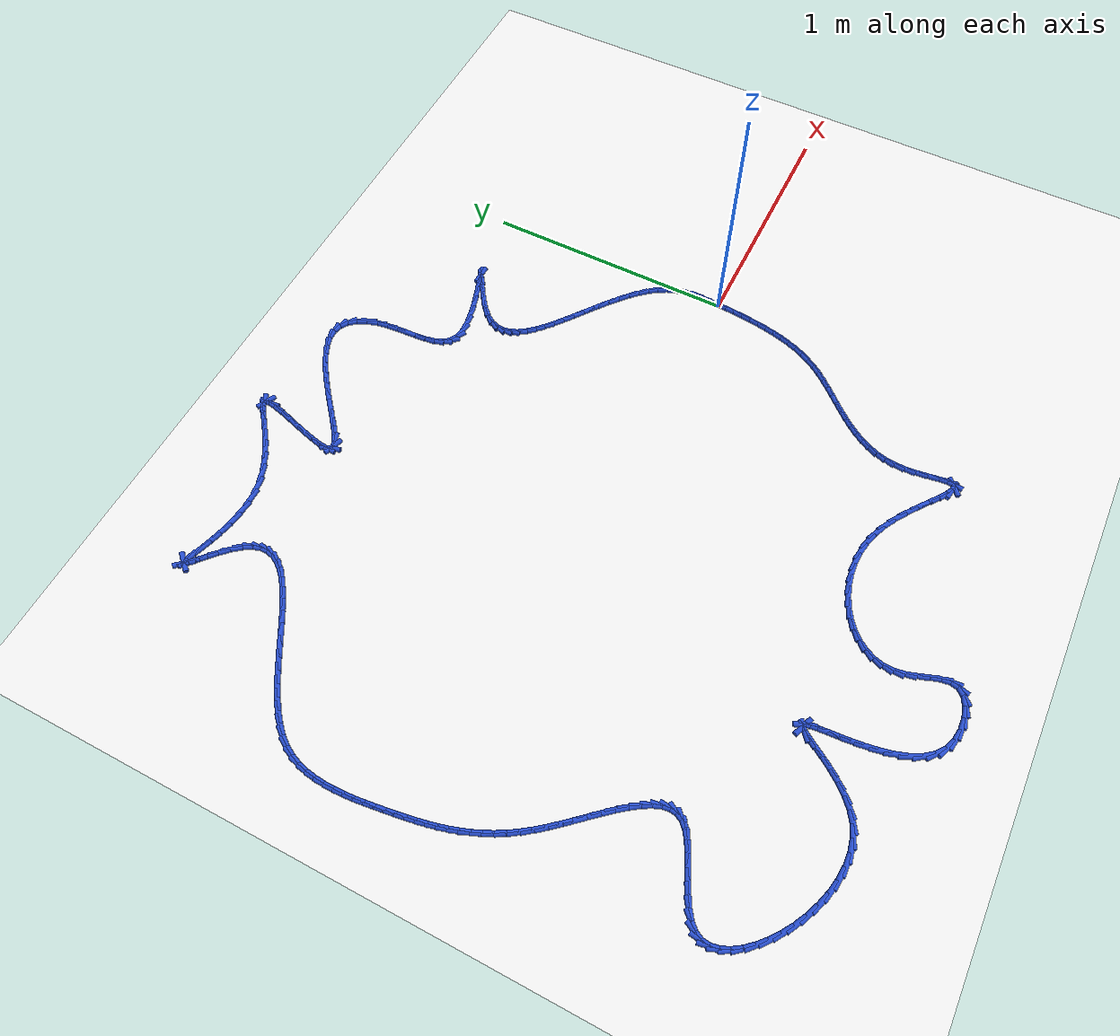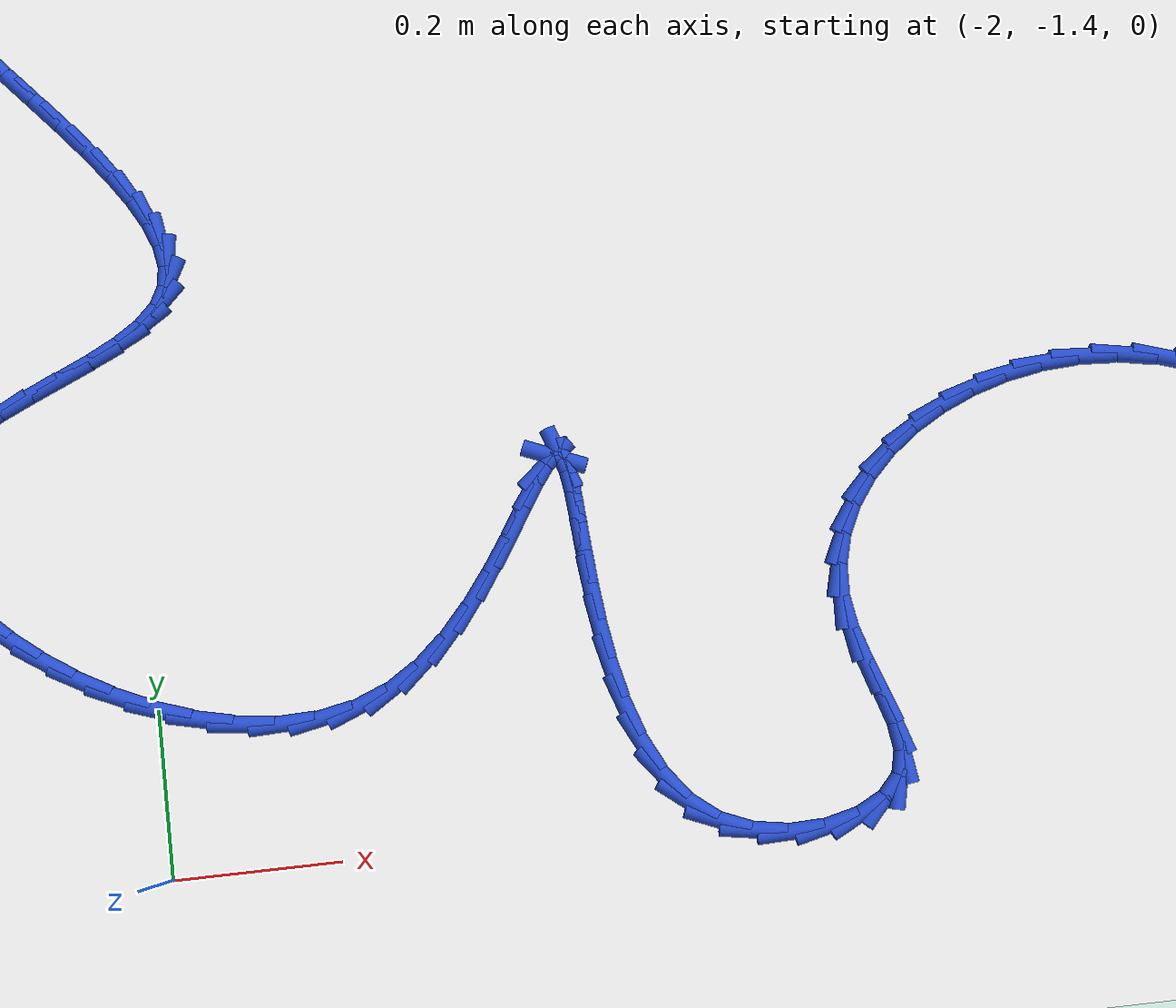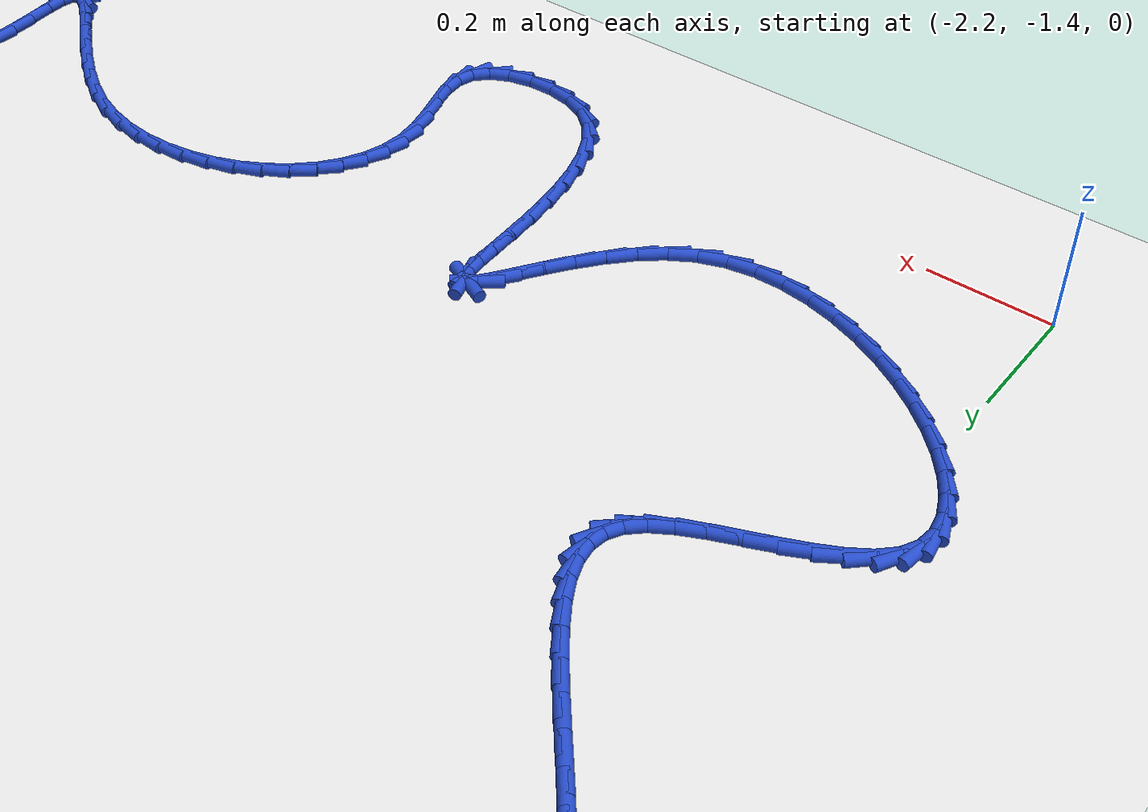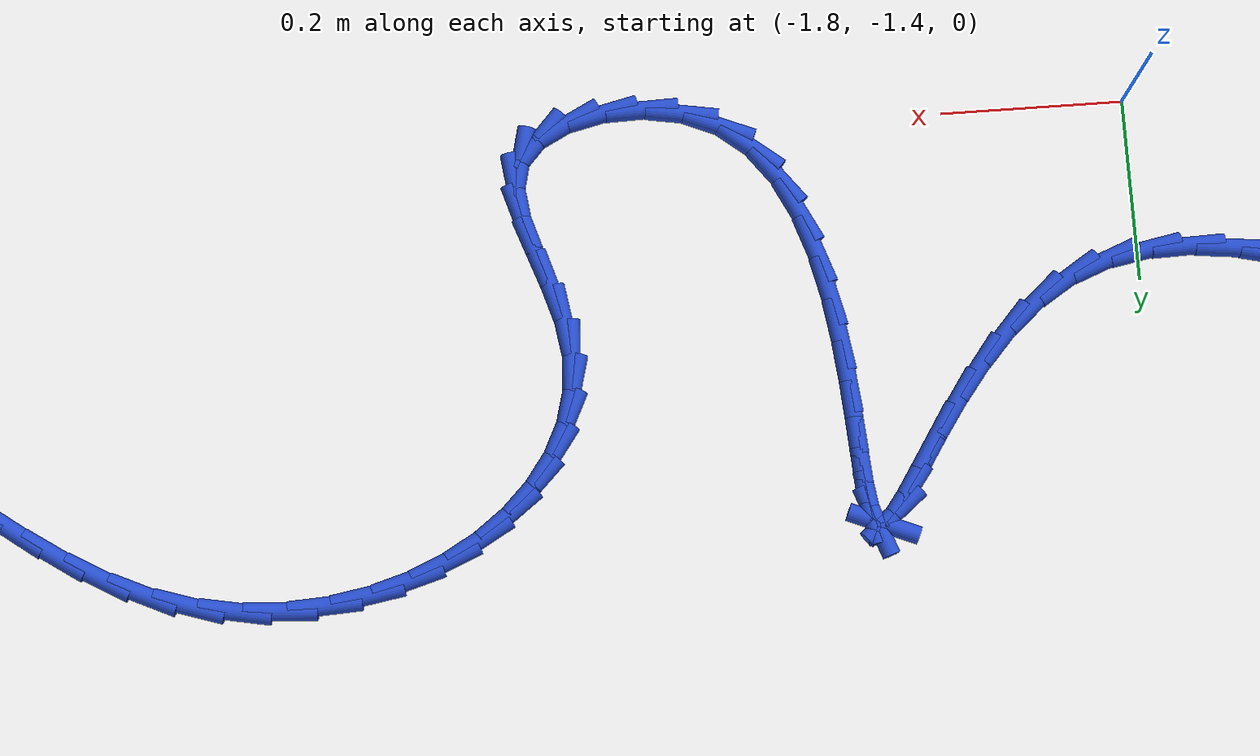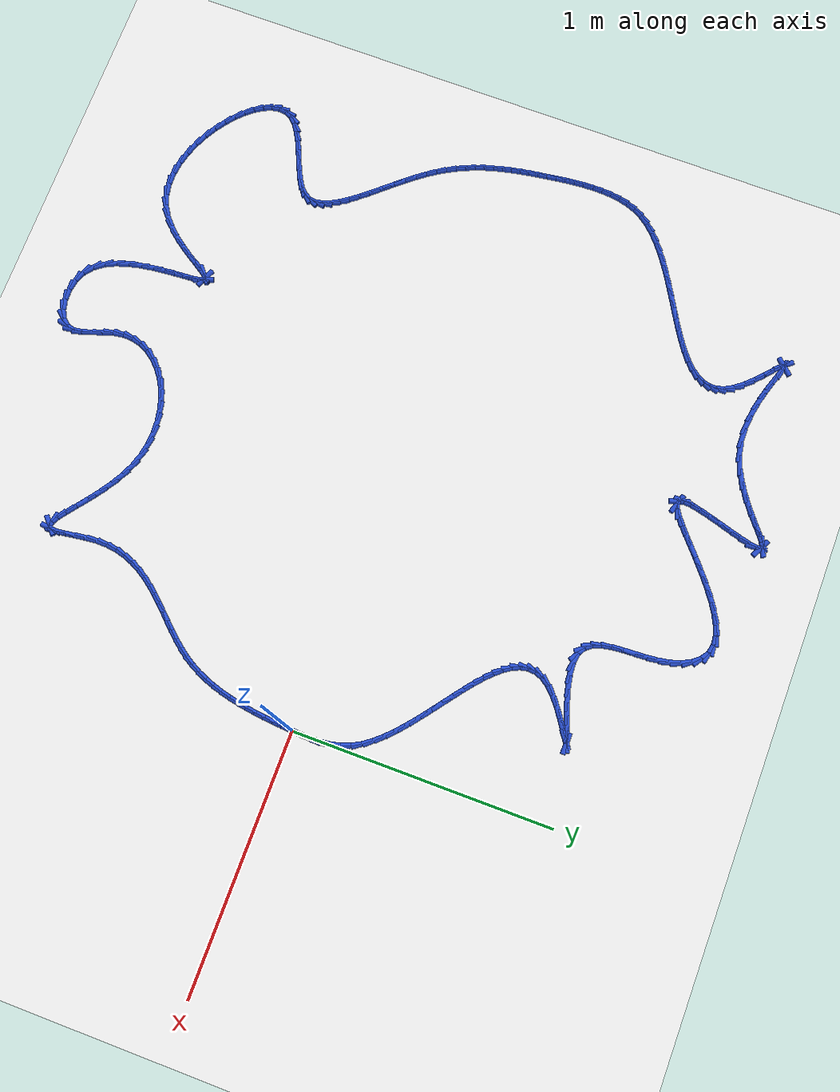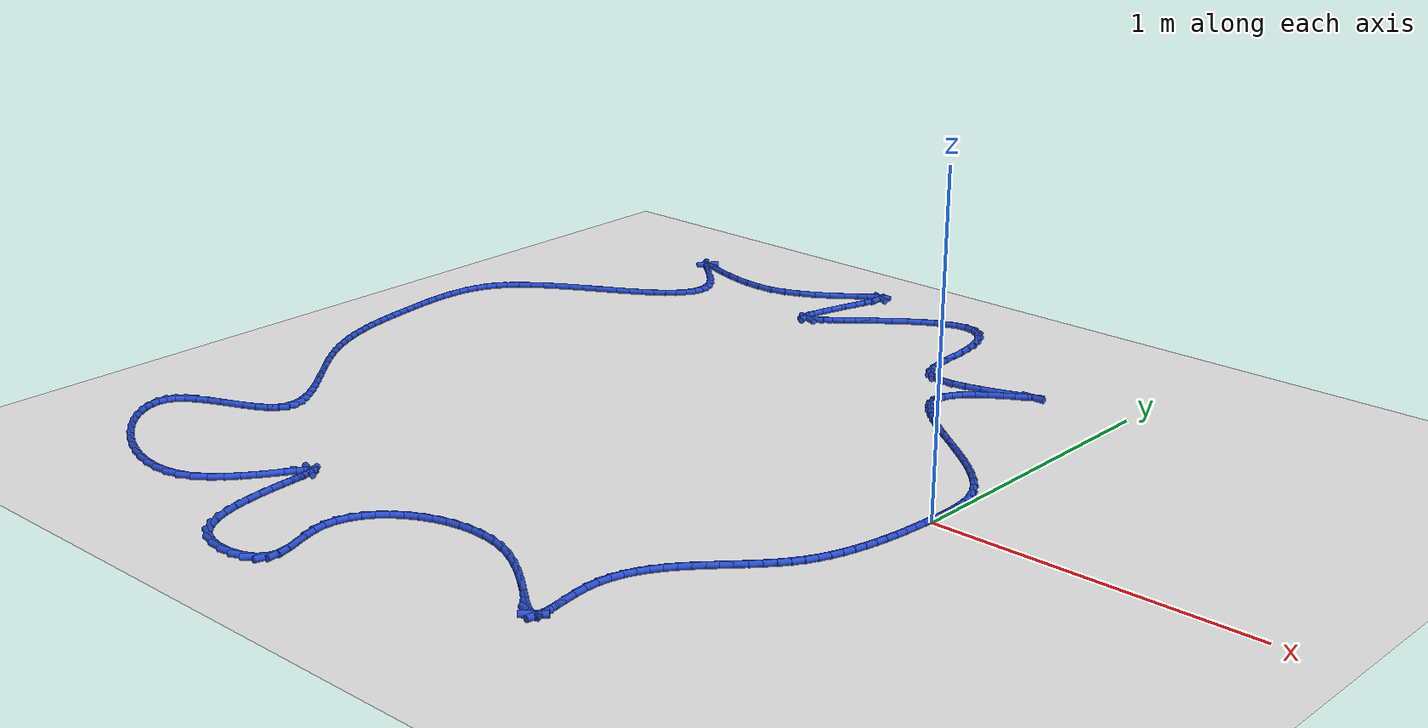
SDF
<sdf version="1.6">
 <world name="default">
  <light name="sun" type="directional">
   <pose>0 0 10 0 -0 0</pose>
   <diffuse>0.8 0.8 0.8 1</diffuse>
   <specular>0.2 0.2 0.2 1</specular>
   <attenuation>
    <range>1000</range>
    <constant>0.9</constant>
    <linear>0.01</linear>
    <quadratic>0.001</quadratic>
   </attenuation>
   <direction>-0.5 0.1 -0.9</direction>
  </light>
  <model name="ground_plane">
   <static>1</static>
   <link name="link">
    <collision name="collision">
     <geometry><plane><normal>0 0 1</normal><size>100 100</size></plane></geometry>
     <surface><friction><ode><mu>100</mu><mu2>50</mu2></ode></friction></surface>
    </collision>
    <visual name="visual">
     <cast_shadows>0</cast_shadows>
     <geometry><plane><normal>0 0 1</normal><size>100 100</size></plane></geometry>
     <material>
      <script><uri>file://media/materials/scripts/gazebo.material</uri><name>Gazebo/WhiteGlow</name></script>
     </material>
    </visual>
   </link>
  </model>
  <gravity>0 0 -9.8</gravity>
  <magnetic_field>6e-06 2.3e-05 -4.2e-05</magnetic_field>
  <atmosphere type="adiabatic"/>
  <physics name="default_physics" default="0" type="ode">
   <max_step_size>0.001</max_step_size>
   <real_time_factor>1</real_time_factor>
   <real_time_update_rate>1000</real_time_update_rate>
  </physics>
  <scene><ambient>0.4 0.4 0.4 1</ambient><background>0.7 0.7 0.7 1</background><shadows>1</shadows></scene>
  <spherical_coordinates>
   <surface_model>EARTH_WGS84</surface_model>
   <latitude_deg>0</latitude_deg>
   <longitude_deg>0</longitude_deg>
   <elevation>0</elevation>
   <heading_deg>0</heading_deg>
  </spherical_coordinates>
  <model name="line">
   <link name="link_0">
    <pose>-2.45029690981724e-17 2.0816681711721685e-17 0.01 0 1.57 1.5136909945468249</pose>
    <collision name="collision">
     <geometry><cylinder><radius>0.01</radius><length>0.08</length></cylinder></geometry>
    </collision>
    <visual name="visual">
     <material>
      <script><name>Gazebo/Blue</name><uri>file://media/materials/scripts/gazebo.material</uri></script>
     </material>
     <geometry><cylinder><radius>0.01</radius><length>0.08</length></cylinder></geometry>
    </visual>
   </link>
   <link name="link_1">
    <pose>0.0021283104545397552 0.03722938613280561 0.01 0 1.57 1.545094357215458</pose>
    <collision name="collision">
     <geometry><cylinder><radius>0.01</radius><length>0.08</length></cylinder></geometry>
    </collision>
    <visual name="visual">
     <material>
      <script><name>Gazebo/Blue</name><uri>file://media/materials/scripts/gazebo.material</uri></script>
     </material>
     <geometry><cylinder><radius>0.01</radius><length>0.08</length></cylinder></geometry>
    </visual>
   </link>
   <link name="link_2">
    <pose>0.0030865516204879313 0.07450396743628847 0.01 0 1.57 -1.5394861746280042</pose>
    <collision name="collision">
     <geometry><cylinder><radius>0.01</radius><length>0.08</length></cylinder></geometry>
    </collision>
    <visual name="visual">
     <material>
      <script><name>Gazebo/Blue</name><uri>file://media/materials/scripts/gazebo.material</uri></script>
     </material>
     <geometry><cylinder><radius>0.01</radius><length>0.08</length></cylinder></geometry>
    </visual>
   </link>
   <link name="link_3">
    <pose>0.001924385931921374 0.11160969246168757 0.01 0 1.57 -1.4560363001852206</pose>
    <collision name="collision">
     <geometry><cylinder><radius>0.01</radius><length>0.08</length></cylinder></geometry>
    </collision>
    <visual name="visual">
     <material>
      <script><name>Gazebo/Blue</name><uri>file://media/materials/scripts/gazebo.material</uri></script>
     </material>
     <geometry><cylinder><radius>0.01</radius><length>0.08</length></cylinder></geometry>
    </visual>
   </link>
   <link name="link_4">
    <pose>-0.0023085241770830506 0.14833250976024182 0.01 0 1.57 -1.346173205877461</pose>
    <collision name="collision">
     <geometry><cylinder><radius>0.01</radius><length>0.08</length></cylinder></geometry>
    </collision>
    <visual name="visual">
     <material>
      <script><name>Gazebo/Blue</name><uri>file://media/materials/scripts/gazebo.material</uri></script>
     </material>
     <geometry><cylinder><radius>0.01</radius><length>0.08</length></cylinder></geometry>
    </visual>
   </link>
   <link name="link_5">
    <pose>-0.010562516272448468 0.1844583678831901 0.01 0 1.57 -1.212464053454606</pose>
    <collision name="collision">
     <geometry><cylinder><radius>0.01</radius><length>0.08</length></cylinder></geometry>
    </collision>
    <visual name="visual">
     <material>
      <script><name>Gazebo/Blue</name><uri>file://media/materials/scripts/gazebo.material</uri></script>
     </material>
     <geometry><cylinder><radius>0.01</radius><length>0.08</length></cylinder></geometry>
    </visual>
   </link>
   <link name="link_6">
    <pose>-0.02378792792009802 0.21977321538177125 0.01 0 1.57 -1.0671118016401824</pose>
    <collision name="collision">
     <geometry><cylinder><radius>0.01</radius><length>0.08</length></cylinder></geometry>
    </collision>
    <visual name="visual">
     <material>
      <script><name>Gazebo/Blue</name><uri>file://media/materials/scripts/gazebo.material</uri></script>
     </material>
     <geometry><cylinder><radius>0.01</radius><length>0.08</length></cylinder></geometry>
    </visual>
   </link>
   <link name="link_7">
    <pose>-0.04270590388653813 0.25410110925956286 0.01 0 1.57 -0.9438012129007117</pose>
    <collision name="collision">
     <geometry><cylinder><radius>0.01</radius><length>0.08</length></cylinder></geometry>
    </collision>
    <visual name="visual">
     <material>
      <script><name>Gazebo/Blue</name><uri>file://media/materials/scripts/gazebo.material</uri></script>
     </material>
     <geometry><cylinder><radius>0.01</radius><length>0.08</length></cylinder></geometry>
    </visual>
   </link>
   <link name="link_8">
    <pose>-0.06687477195608788 0.28745945096925546 0.01 0 1.57 -0.8484661515114426</pose>
    <collision name="collision">
     <geometry><cylinder><radius>0.01</radius><length>0.08</length></cylinder></geometry>
    </collision>
    <visual name="visual">
     <material>
      <script><name>Gazebo/Blue</name><uri>file://media/materials/scripts/gazebo.material</uri></script>
     </material>
     <geometry><cylinder><radius>0.01</radius><length>0.08</length></cylinder></geometry>
    </visual>
   </link>
   <link name="link_9">
    <pose>-0.09548497718444317 0.319926810732653 0.01 0 1.57 -0.7762137547601449</pose>
    <collision name="collision">
     <geometry><cylinder><radius>0.01</radius><length>0.08</length></cylinder></geometry>
    </collision>
    <visual name="visual">
     <material>
      <script><name>Gazebo/Blue</name><uri>file://media/materials/scripts/gazebo.material</uri></script>
     </material>
     <geometry><cylinder><radius>0.01</radius><length>0.08</length></cylinder></geometry>
    </visual>
   </link>
   <link name="link_10">
    <pose>-0.12772682019952733 0.3515817827859215 0.01 0 1.57 -0.7226994354463756</pose>
    <collision name="collision">
     <geometry><cylinder><radius>0.01</radius><length>0.08</length></cylinder></geometry>
    </collision>
    <visual name="visual">
     <material>
      <script><name>Gazebo/Blue</name><uri>file://media/materials/scripts/gazebo.material</uri></script>
     </material>
     <geometry><cylinder><radius>0.01</radius><length>0.08</length></cylinder></geometry>
    </visual>
   </link>
   <link name="link_11">
    <pose>-0.1627906016292635 0.38250296136522677 0.01 0 1.57 -0.6846145775217288</pose>
    <collision name="collision">
     <geometry><cylinder><radius>0.01</radius><length>0.08</length></cylinder></geometry>
    </collision>
    <visual name="visual">
     <material>
      <script><name>Gazebo/Blue</name><uri>file://media/materials/scripts/gazebo.material</uri></script>
     </material>
     <geometry><cylinder><radius>0.01</radius><length>0.08</length></cylinder></geometry>
    </visual>
   </link>
   <link name="link_12">
    <pose>-0.19986662210157494 0.4127689407067348 0.01 0 1.57 -0.659693345565341</pose>
    <collision name="collision">
     <geometry><cylinder><radius>0.01</radius><length>0.08</length></cylinder></geometry>
    </collision>
    <visual name="visual">
     <material>
      <script><name>Gazebo/Blue</name><uri>file://media/materials/scripts/gazebo.material</uri></script>
     </material>
     <geometry><cylinder><radius>0.01</radius><length>0.08</length></cylinder></geometry>
    </visual>
   </link>
   <link name="link_13">
    <pose>-0.2381451822443848 0.4424583150466118 0.01 0 1.57 -0.646602122247678</pose>
    <collision name="collision">
     <geometry><cylinder><radius>0.01</radius><length>0.08</length></cylinder></geometry>
    </collision>
    <visual name="visual">
     <material>
      <script><name>Gazebo/Blue</name><uri>file://media/materials/scripts/gazebo.material</uri></script>
     </material>
     <geometry><cylinder><radius>0.01</radius><length>0.08</length></cylinder></geometry>
    </visual>
   </link>
   <link name="link_14">
    <pose>-0.27681658268561626 0.4716496786210234 0.01 0 1.57 -0.644855550162026</pose>
    <collision name="collision">
     <geometry><cylinder><radius>0.01</radius><length>0.08</length></cylinder></geometry>
    </collision>
    <visual name="visual">
     <material>
      <script><name>Gazebo/Blue</name><uri>file://media/materials/scripts/gazebo.material</uri></script>
     </material>
     <geometry><cylinder><radius>0.01</radius><length>0.08</length></cylinder></geometry>
    </visual>
   </link>
   <link name="link_15">
    <pose>-0.3150711240531926 0.5004216256661359 0.01 0 1.57 -0.6548137804907926</pose>
    <collision name="collision">
     <geometry><cylinder><radius>0.01</radius><length>0.08</length></cylinder></geometry>
    </collision>
    <visual name="visual">
     <material>
      <script><name>Gazebo/Blue</name><uri>file://media/materials/scripts/gazebo.material</uri></script>
     </material>
     <geometry><cylinder><radius>0.01</radius><length>0.08</length></cylinder></geometry>
    </visual>
   </link>
   <link name="link_16">
    <pose>-0.3520991069750369 0.5288527504181149 0.01 0 1.57 -0.67779197126777</pose>
    <collision name="collision">
     <geometry><cylinder><radius>0.01</radius><length>0.08</length></cylinder></geometry>
    </collision>
    <visual name="visual">
     <material>
      <script><name>Gazebo/Blue</name><uri>file://media/materials/scripts/gazebo.material</uri></script>
     </material>
     <geometry><cylinder><radius>0.01</radius><length>0.08</length></cylinder></geometry>
    </visual>
   </link>
   <link name="link_17">
    <pose>-0.3870908320790724 0.5570216471131264 0.01 0 1.57 -0.7163176116048785</pose>
    <collision name="collision">
     <geometry><cylinder><radius>0.01</radius><length>0.08</length></cylinder></geometry>
    </collision>
    <visual name="visual">
     <material>
      <script><name>Gazebo/Blue</name><uri>file://media/materials/scripts/gazebo.material</uri></script>
     </material>
     <geometry><cylinder><radius>0.01</radius><length>0.08</length></cylinder></geometry>
    </visual>
   </link>
   <link name="link_18">
    <pose>-0.41923659999322227 0.5850069099873364 0.01 0 1.57 -0.7745792766399525</pose>
    <collision name="collision">
     <geometry><cylinder><radius>0.01</radius><length>0.08</length></cylinder></geometry>
    </collision>
    <visual name="visual">
     <material>
      <script><name>Gazebo/Blue</name><uri>file://media/materials/scripts/gazebo.material</uri></script>
     </material>
     <geometry><cylinder><radius>0.01</radius><length>0.08</length></cylinder></geometry>
    </visual>
   </link>
   <link name="link_19">
    <pose>-0.44772671134541 0.6128871332769112 0.01 0 1.57 -0.8590720318524332</pose>
    <collision name="collision">
     <geometry><cylinder><radius>0.01</radius><length>0.08</length></cylinder></geometry>
    </collision>
    <visual name="visual">
     <material>
      <script><name>Gazebo/Blue</name><uri>file://media/materials/scripts/gazebo.material</uri></script>
     </material>
     <geometry><cylinder><radius>0.01</radius><length>0.08</length></cylinder></geometry>
    </visual>
   </link>
   <link name="link_20">
    <pose>-0.4717514667635585 0.6407409112180167 0.01 0 1.57 -0.9791866043591809</pose>
    <collision name="collision">
     <geometry><cylinder><radius>0.01</radius><length>0.08</length></cylinder></geometry>
    </collision>
    <visual name="visual">
     <material>
      <script><name>Gazebo/Blue</name><uri>file://media/materials/scripts/gazebo.material</uri></script>
     </material>
     <geometry><cylinder><radius>0.01</radius><length>0.08</length></cylinder></geometry>
    </visual>
   </link>
   <link name="link_21">
    <pose>-0.49050116687559087 0.6686468380468182 0.01 0 1.57 -1.14650642508544</pose>
    <collision name="collision">
     <geometry><cylinder><radius>0.01</radius><length>0.08</length></cylinder></geometry>
    </collision>
    <visual name="visual">
     <material>
      <script><name>Gazebo/Blue</name><uri>file://media/materials/scripts/gazebo.material</uri></script>
     </material>
     <geometry><cylinder><radius>0.01</radius><length>0.08</length></cylinder></geometry>
    </visual>
   </link>
   <link name="link_22">
    <pose>-0.5031661123094305 0.6966835079994823 0.01 0 1.57 -1.369275297648172</pose>
    <collision name="collision">
     <geometry><cylinder><radius>0.01</radius><length>0.08</length></cylinder></geometry>
    </collision>
    <visual name="visual">
     <material>
      <script><name>Gazebo/Blue</name><uri>file://media/materials/scripts/gazebo.material</uri></script>
     </material>
     <geometry><cylinder><radius>0.01</radius><length>0.08</length></cylinder></geometry>
    </visual>
   </link>
   <link name="link_23">
    <pose>-0.5089366036930008 0.7249295153121751 0.01 0 1.57 1.5031326881236624</pose>
    <collision name="collision">
     <geometry><cylinder><radius>0.01</radius><length>0.08</length></cylinder></geometry>
    </collision>
    <visual name="visual">
     <material>
      <script><name>Gazebo/Blue</name><uri>file://media/materials/scripts/gazebo.material</uri></script>
     </material>
     <geometry><cylinder><radius>0.01</radius><length>0.08</length></cylinder></geometry>
    </visual>
   </link>
   <link name="link_24">
    <pose>-0.5070029416542247 0.753463454221062 0.01 0 1.57 1.2239135748374024</pose>
    <collision name="collision">
     <geometry><cylinder><radius>0.01</radius><length>0.08</length></cylinder></geometry>
    </collision>
    <visual name="visual">
     <material>
      <script><name>Gazebo/Blue</name><uri>file://media/materials/scripts/gazebo.material</uri></script>
     </material>
     <geometry><cylinder><radius>0.01</radius><length>0.08</length></cylinder></geometry>
    </visual>
   </link>
   <link name="link_25">
    <pose>-0.4965554268210252 0.7823639189623093 0.01 0 1.57 0.9779181011260594</pose>
    <collision name="collision">
     <geometry><cylinder><radius>0.01</radius><length>0.08</length></cylinder></geometry>
    </collision>
    <visual name="visual">
     <material>
      <script><name>Gazebo/Blue</name><uri>file://media/materials/scripts/gazebo.material</uri></script>
     </material>
     <geometry><cylinder><radius>0.01</radius><length>0.08</length></cylinder></geometry>
    </visual>
   </link>
   <link name="link_26">
    <pose>-0.47678435982132594 0.811709503772083 0.01 0 1.57 0.7888293519062755</pose>
    <collision name="collision">
     <geometry><cylinder><radius>0.01</radius><length>0.08</length></cylinder></geometry>
    </collision>
    <visual name="visual">
     <material>
      <script><name>Gazebo/Blue</name><uri>file://media/materials/scripts/gazebo.material</uri></script>
     </material>
     <geometry><cylinder><radius>0.01</radius><length>0.08</length></cylinder></geometry>
    </visual>
   </link>
   <link name="link_27">
    <pose>-0.4472249907502722 0.8414724195841345 0.01 0 1.57 0.675325815892175</pose>
    <collision name="collision">
     <geometry><cylinder><radius>0.01</radius><length>0.08</length></cylinder></geometry>
    </collision>
    <visual name="visual">
     <material>
      <script><name>Gazebo/Blue</name><uri>file://media/materials/scripts/gazebo.material</uri></script>
     </material>
     <geometry><cylinder><radius>0.01</radius><length>0.08</length></cylinder></geometry>
    </visual>
   </link>
   <link name="link_28">
    <pose>-0.4109363943716504 0.8705381207461117 0.01 0 1.57 0.612323316226513</pose>
    <collision name="collision">
     <geometry><cylinder><radius>0.01</radius><length>0.08</length></cylinder></geometry>
    </collision>
    <visual name="visual">
     <material>
      <script><name>Gazebo/Blue</name><uri>file://media/materials/scripts/gazebo.material</uri></script>
     </material>
     <geometry><cylinder><radius>0.01</radius><length>0.08</length></cylinder></geometry>
    </visual>
   </link>
   <link name="link_29">
    <pose>-0.3730396628283028 0.897156130145366 0.01 0 1.57 0.5779954486199383</pose>
    <collision name="collision">
     <geometry><cylinder><radius>0.01</radius><length>0.08</length></cylinder></geometry>
    </collision>
    <visual name="visual">
     <material>
      <script><name>Gazebo/Blue</name><uri>file://media/materials/scripts/gazebo.material</uri></script>
     </material>
     <geometry><cylinder><radius>0.01</radius><length>0.08</length></cylinder></geometry>
    </visual>
   </link>
   <link name="link_30">
    <pose>-0.33868189373416085 0.9195679505151154 0.01 0 1.57 0.5697894702301494</pose>
    <collision name="collision">
     <geometry><cylinder><radius>0.01</radius><length>0.08</length></cylinder></geometry>
    </collision>
    <visual name="visual">
     <material>
      <script><name>Gazebo/Blue</name><uri>file://media/materials/scripts/gazebo.material</uri></script>
     </material>
     <geometry><cylinder><radius>0.01</radius><length>0.08</length></cylinder></geometry>
    </visual>
   </link>
   <link name="link_31">
    <pose>-0.3130101847031565 0.936015084588579 0.01 0 1.57 0.6350695238382865</pose>
    <collision name="collision">
     <geometry><cylinder><radius>0.01</radius><length>0.08</length></cylinder></geometry>
    </collision>
    <visual name="visual">
     <material>
      <script><name>Gazebo/Blue</name><uri>file://media/materials/scripts/gazebo.material</uri></script>
     </material>
     <geometry><cylinder><radius>0.01</radius><length>0.08</length></cylinder></geometry>
    </visual>
   </link>
   <link name="link_32">
    <pose>-0.30117153573722155 0.9447390812265715 0.01 0 1.57 0.0011852686835323186</pose>
    <collision name="collision">
     <geometry><cylinder><radius>0.01</radius><length>0.08</length></cylinder></geometry>
    </collision>
    <visual name="visual">
     <material>
      <script><name>Gazebo/Blue</name><uri>file://media/materials/scripts/gazebo.material</uri></script>
     </material>
     <geometry><cylinder><radius>0.01</radius><length>0.08</length></cylinder></geometry>
    </visual>
   </link>
   <link name="link_33">
    <pose>-0.3067237095459434 0.9447325004057487 0.01 0 1.57 0.327273909749804</pose>
    <collision name="collision">
     <geometry><cylinder><radius>0.01</radius><length>0.08</length></cylinder></geometry>
    </collision>
    <visual name="visual">
     <material>
      <script><name>Gazebo/Blue</name><uri>file://media/materials/scripts/gazebo.material</uri></script>
     </material>
     <geometry><cylinder><radius>0.01</radius><length>0.08</length></cylinder></geometry>
    </visual>
   </link>
   <link name="link_34">
    <pose>-0.32760319297617624 0.9376442962601772 0.01 0 1.57 0.3479606941858133</pose>
    <collision name="collision">
     <geometry><cylinder><radius>0.01</radius><length>0.08</length></cylinder></geometry>
    </collision>
    <visual name="visual">
     <material>
      <script><name>Gazebo/Blue</name><uri>file://media/materials/scripts/gazebo.material</uri></script>
     </material>
     <geometry><cylinder><radius>0.01</radius><length>0.08</length></cylinder></geometry>
    </visual>
   </link>
   <link name="link_35">
    <pose>-0.36050421985342607 0.925710462903549 0.01 0 1.57 0.3361949558112934</pose>
    <collision name="collision">
     <geometry><cylinder><radius>0.01</radius><length>0.08</length></cylinder></geometry>
    </collision>
    <visual name="visual">
     <material>
      <script><name>Gazebo/Blue</name><uri>file://media/materials/scripts/gazebo.material</uri></script>
     </material>
     <geometry><cylinder><radius>0.01</radius><length>0.08</length></cylinder></geometry>
    </visual>
   </link>
   <link name="link_36">
    <pose>-0.4021210240031986 0.9111669944495564 0.01 0 1.57 0.3071649054956794</pose>
    <collision name="collision">
     <geometry><cylinder><radius>0.01</radius><length>0.08</length></cylinder></geometry>
    </collision>
    <visual name="visual">
     <material>
      <script><name>Gazebo/Blue</name><uri>file://media/materials/scripts/gazebo.material</uri></script>
     </material>
     <geometry><cylinder><radius>0.01</radius><length>0.08</length></cylinder></geometry>
    </visual>
   </link>
   <link name="link_37">
    <pose>-0.4491478392510006 0.8962498850118914 0.01 0 1.57 0.2597117311935772</pose>
    <collision name="collision">
     <geometry><cylinder><radius>0.01</radius><length>0.08</length></cylinder></geometry>
    </collision>
    <visual name="visual">
     <material>
      <script><name>Gazebo/Blue</name><uri>file://media/materials/scripts/gazebo.material</uri></script>
     </material>
     <geometry><cylinder><radius>0.01</radius><length>0.08</length></cylinder></geometry>
    </visual>
   </link>
   <link name="link_38">
    <pose>-0.4982788994223373 0.883195128704247 0.01 0 1.57 0.18473556994100826</pose>
    <collision name="collision">
     <geometry><cylinder><radius>0.01</radius><length>0.08</length></cylinder></geometry>
    </collision>
    <visual name="visual">
     <material>
      <script><name>Gazebo/Blue</name><uri>file://media/materials/scripts/gazebo.material</uri></script>
     </material>
     <geometry><cylinder><radius>0.01</radius><length>0.08</length></cylinder></geometry>
    </visual>
   </link>
   <link name="link_39">
    <pose>-0.5462084383427154 0.8742387196403149 0.01 0 1.57 0.06031211058189526</pose>
    <collision name="collision">
     <geometry><cylinder><radius>0.01</radius><length>0.08</length></cylinder></geometry>
    </collision>
    <visual name="visual">
     <material>
      <script><name>Gazebo/Blue</name><uri>file://media/materials/scripts/gazebo.material</uri></script>
     </material>
     <geometry><cylinder><radius>0.01</radius><length>0.08</length></cylinder></geometry>
    </visual>
   </link>
   <link name="link_40">
    <pose>-0.58963068983764 0.8716166519337875 0.01 0 1.57 -0.16489002332715347</pose>
    <collision name="collision">
     <geometry><cylinder><radius>0.01</radius><length>0.08</length></cylinder></geometry>
    </collision>
    <visual name="visual">
     <material>
      <script><name>Gazebo/Blue</name><uri>file://media/materials/scripts/gazebo.material</uri></script>
     </material>
     <geometry><cylinder><radius>0.01</radius><length>0.08</length></cylinder></geometry>
    </visual>
   </link>
   <link name="link_41">
    <pose>-0.6252652395317398 0.8775462709072951 0.01 0 1.57 -0.5295911473238184</pose>
    <collision name="collision">
     <geometry><cylinder><radius>0.01</radius><length>0.08</length></cylinder></geometry>
    </collision>
    <visual name="visual">
     <material>
      <script><name>Gazebo/Blue</name><uri>file://media/materials/scripts/gazebo.material</uri></script>
     </material>
     <geometry><cylinder><radius>0.01</radius><length>0.08</length></cylinder></geometry>
    </visual>
   </link>
   <link name="link_42">
    <pose>-0.6515866346845763 0.8929539715767156 0.01 0 1.57 -0.9121462160667123</pose>
    <collision name="collision">
     <geometry><cylinder><radius>0.01</radius><length>0.08</length></cylinder></geometry>
    </collision>
    <visual name="visual">
     <material>
      <script><name>Gazebo/Blue</name><uri>file://media/materials/scripts/gazebo.material</uri></script>
     </material>
     <geometry><cylinder><radius>0.01</radius><length>0.08</length></cylinder></geometry>
    </visual>
   </link>
   <link name="link_43">
    <pose>-0.6699333479227746 0.9166594445961198 0.01 0 1.57 -1.1981117698360868</pose>
    <collision name="collision">
     <geometry><cylinder><radius>0.01</radius><length>0.08</length></cylinder></geometry>
    </collision>
    <visual name="visual">
     <material>
      <script><name>Gazebo/Blue</name><uri>file://media/materials/scripts/gazebo.material</uri></script>
     </material>
     <geometry><cylinder><radius>0.01</radius><length>0.08</length></cylinder></geometry>
    </visual>
   </link>
   <link name="link_44">
    <pose>-0.6819078115934324 0.9472882117697693 0.01 0 1.57 -1.3742213780564057</pose>
    <collision name="collision">
     <geometry><cylinder><radius>0.01</radius><length>0.08</length></cylinder></geometry>
    </collision>
    <visual name="visual">
     <material>
      <script><name>Gazebo/Blue</name><uri>file://media/materials/scripts/gazebo.material</uri></script>
     </material>
     <geometry><cylinder><radius>0.01</radius><length>0.08</length></cylinder></geometry>
    </visual>
   </link>
   <link name="link_45">
    <pose>-0.6891124580436467 0.9834657949019259 0.01 0 1.57 -1.4710768963742054</pose>
    <collision name="collision">
     <geometry><cylinder><radius>0.01</radius><length>0.08</length></cylinder></geometry>
    </collision>
    <visual name="visual">
     <material>
      <script><name>Gazebo/Blue</name><uri>file://media/materials/scripts/gazebo.material</uri></script>
     </material>
     <geometry><cylinder><radius>0.01</radius><length>0.08</length></cylinder></geometry>
    </visual>
   </link>
   <link name="link_46">
    <pose>-0.693149719620515 1.0238177157968509 0.01 0 1.57 -1.5135655659652048</pose>
    <collision name="collision">
     <geometry><cylinder><radius>0.01</radius><length>0.08</length></cylinder></geometry>
    </collision>
    <visual name="visual">
     <material>
      <script><name>Gazebo/Blue</name><uri>file://media/materials/scripts/gazebo.material</uri></script>
     </material>
     <geometry><cylinder><radius>0.01</radius><length>0.08</length></cylinder></geometry>
    </visual>
   </link>
   <link name="link_47">
    <pose>-0.6956220286711351 1.0669694962588065 0.01 0 1.57 -1.5145535816327758</pose>
    <collision name="collision">
     <geometry><cylinder><radius>0.01</radius><length>0.08</length></cylinder></geometry>
    </collision>
    <visual name="visual">
     <material>
      <script><name>Gazebo/Blue</name><uri>file://media/materials/scripts/gazebo.material</uri></script>
     </material>
     <geometry><cylinder><radius>0.01</radius><length>0.08</length></cylinder></geometry>
    </visual>
   </link>
   <link name="link_48">
    <pose>-0.6981318175426041 1.1115466580920546 0.01 0 1.57 -1.478078813758545</pose>
    <collision name="collision">
     <geometry><cylinder><radius>0.01</radius><length>0.08</length></cylinder></geometry>
    </collision>
    <visual name="visual">
     <material>
      <script><name>Gazebo/Blue</name><uri>file://media/materials/scripts/gazebo.material</uri></script>
     </material>
     <geometry><cylinder><radius>0.01</radius><length>0.08</length></cylinder></geometry>
    </visual>
   </link>
   <link name="link_49">
    <pose>-0.7022815185820194 1.1561747231008557 0.01 0 1.57 -1.4017266032522229</pose>
    <collision name="collision">
     <geometry><cylinder><radius>0.01</radius><length>0.08</length></cylinder></geometry>
    </collision>
    <visual name="visual">
     <material>
      <script><name>Gazebo/Blue</name><uri>file://media/materials/scripts/gazebo.material</uri></script>
     </material>
     <geometry><cylinder><radius>0.01</radius><length>0.08</length></cylinder></geometry>
    </visual>
   </link>
   <link name="link_50">
    <pose>-0.7096735641364784 1.1994792130894725 0.01 0 1.57 -1.2781310200550338</pose>
    <collision name="collision">
     <geometry><cylinder><radius>0.01</radius><length>0.08</length></cylinder></geometry>
    </collision>
    <visual name="visual">
     <material>
      <script><name>Gazebo/Blue</name><uri>file://media/materials/scripts/gazebo.material</uri></script>
     </material>
     <geometry><cylinder><radius>0.01</radius><length>0.08</length></cylinder></geometry>
    </visual>
   </link>
   <link name="link_51">
    <pose>-0.7219086950805731 1.2400846227256874 0.01 0 1.57 -1.1069989036670076</pose>
    <collision name="collision">
     <geometry><cylinder><radius>0.01</radius><length>0.08</length></cylinder></geometry>
    </collision>
    <visual name="visual">
     <material>
      <script><name>Gazebo/Blue</name><uri>file://media/materials/scripts/gazebo.material</uri></script>
     </material>
     <geometry><cylinder><radius>0.01</radius><length>0.08</length></cylinder></geometry>
    </visual>
   </link>
   <link name="link_52">
    <pose>-0.7400035297305314 1.2762607417762513 0.01 0 1.57 -0.8914880120880703</pose>
    <collision name="collision">
     <geometry><cylinder><radius>0.01</radius><length>0.08</length></cylinder></geometry>
    </collision>
    <visual name="visual">
     <material>
      <script><name>Gazebo/Blue</name><uri>file://media/materials/scripts/gazebo.material</uri></script>
     </material>
     <geometry><cylinder><radius>0.01</radius><length>0.08</length></cylinder></geometry>
    </visual>
   </link>
   <link name="link_53">
    <pose>-0.7635379911036551 1.3054049354515875 0.01 0 1.57 -0.5997950704235611</pose>
    <collision name="collision">
     <geometry><cylinder><radius>0.01</radius><length>0.08</length></cylinder></geometry>
    </collision>
    <visual name="visual">
     <material>
      <script><name>Gazebo/Blue</name><uri>file://media/materials/scripts/gazebo.material</uri></script>
     </material>
     <geometry><cylinder><radius>0.01</radius><length>0.08</length></cylinder></geometry>
    </visual>
   </link>
   <link name="link_54">
    <pose>-0.7918750884386484 1.3247828628877072 0.01 0 1.57 -0.2316319192950246</pose>
    <collision name="collision">
     <geometry><cylinder><radius>0.01</radius><length>0.08</length></cylinder></geometry>
    </collision>
    <visual name="visual">
     <material>
      <script><name>Gazebo/Blue</name><uri>file://media/materials/scripts/gazebo.material</uri></script>
     </material>
     <geometry><cylinder><radius>0.01</radius><length>0.08</length></cylinder></geometry>
    </visual>
   </link>
   <link name="link_55">
    <pose>-0.8243574146994715 1.3324443200263412 0.01 0 1.57 0.08634510716277952</pose>
    <collision name="collision">
     <geometry><cylinder><radius>0.01</radius><length>0.08</length></cylinder></geometry>
    </collision>
    <visual name="visual">
     <material>
      <script><name>Gazebo/Blue</name><uri>file://media/materials/scripts/gazebo.material</uri></script>
     </material>
     <geometry><cylinder><radius>0.01</radius><length>0.08</length></cylinder></geometry>
    </visual>
   </link>
   <link name="link_56">
    <pose>-0.8602521045232228 1.32933726381711 0.01 0 1.57 0.30782062605455734</pose>
    <collision name="collision">
     <geometry><cylinder><radius>0.01</radius><length>0.08</length></cylinder></geometry>
    </collision>
    <visual name="visual">
     <material>
      <script><name>Gazebo/Blue</name><uri>file://media/materials/scripts/gazebo.material</uri></script>
     </material>
     <geometry><cylinder><radius>0.01</radius><length>0.08</length></cylinder></geometry>
    </visual>
   </link>
   <link name="link_57">
    <pose>-0.8988088633813948 1.3170790608064527 0.01 0 1.57 0.45486618898904807</pose>
    <collision name="collision">
     <geometry><cylinder><radius>0.01</radius><length>0.08</length></cylinder></geometry>
    </collision>
    <visual name="visual">
     <material>
      <script><name>Gazebo/Blue</name><uri>file://media/materials/scripts/gazebo.material</uri></script>
     </material>
     <geometry><cylinder><radius>0.01</radius><length>0.08</length></cylinder></geometry>
    </visual>
   </link>
   <link name="link_58">
    <pose>-0.9392773967454789 1.2972870775408096 0.01 0 1.57 0.5532202787380017</pose>
    <collision name="collision">
     <geometry><cylinder><radius>0.01</radius><length>0.08</length></cylinder></geometry>
    </collision>
    <visual name="visual">
     <material>
      <script><name>Gazebo/Blue</name><uri>file://media/materials/scripts/gazebo.material</uri></script>
     </material>
     <geometry><cylinder><radius>0.01</radius><length>0.08</length></cylinder></geometry>
    </visual>
   </link>
   <link name="link_59">
    <pose>-0.9809074100869686 1.2715786805666203 0.01 0 1.57 0.6199031521513331</pose>
    <collision name="collision">
     <geometry><cylinder><radius>0.01</radius><length>0.08</length></cylinder></geometry>
    </collision>
    <visual name="visual">
     <material>
      <script><name>Gazebo/Blue</name><uri>file://media/materials/scripts/gazebo.material</uri></script>
     </material>
     <geometry><cylinder><radius>0.01</radius><length>0.08</length></cylinder></geometry>
    </visual>
   </link>
   <link name="link_60">
    <pose>-1.022948608877355 1.2415712364303242 0.01 0 1.57 0.6648294993551235</pose>
    <collision name="collision">
     <geometry><cylinder><radius>0.01</radius><length>0.08</length></cylinder></geometry>
    </collision>
    <visual name="visual">
     <material>
      <script><name>Gazebo/Blue</name><uri>file://media/materials/scripts/gazebo.material</uri></script>
     </material>
     <geometry><cylinder><radius>0.01</radius><length>0.08</length></cylinder></geometry>
    </visual>
   </link>
   <link name="link_61">
    <pose>-1.0646506985881314 1.2088821116783612 0.01 0 1.57 0.6934222231570188</pose>
    <collision name="collision">
     <geometry><cylinder><radius>0.01</radius><length>0.08</length></cylinder></geometry>
    </collision>
    <visual name="visual">
     <material>
      <script><name>Gazebo/Blue</name><uri>file://media/materials/scripts/gazebo.material</uri></script>
     </material>
     <geometry><cylinder><radius>0.01</radius><length>0.08</length></cylinder></geometry>
    </visual>
   </link>
   <link name="link_62">
    <pose>-1.1052633846907889 1.1751286728571713 0.01 0 1.57 0.7081264490205855</pose>
    <collision name="collision">
     <geometry><cylinder><radius>0.01</radius><length>0.08</length></cylinder></geometry>
    </collision>
    <visual name="visual">
     <material>
      <script><name>Gazebo/Blue</name><uri>file://media/materials/scripts/gazebo.material</uri></script>
     </material>
     <geometry><cylinder><radius>0.01</radius><length>0.08</length></cylinder></geometry>
    </visual>
   </link>
   <link name="link_63">
    <pose>-1.144036372656821 1.1419282865131943 0.01 0 1.57 0.7088806735255654</pose>
    <collision name="collision">
     <geometry><cylinder><radius>0.01</radius><length>0.08</length></cylinder></geometry>
    </collision>
    <visual name="visual">
     <material>
      <script><name>Gazebo/Blue</name><uri>file://media/materials/scripts/gazebo.material</uri></script>
     </material>
     <geometry><cylinder><radius>0.01</radius><length>0.08</length></cylinder></geometry>
    </visual>
   </link>
   <link name="link_64">
    <pose>-1.1802193679577193 1.1108983191928699 0.01 0 1.57 0.6924564770508023</pose>
    <collision name="collision">
     <geometry><cylinder><radius>0.01</radius><length>0.08</length></cylinder></geometry>
    </collision>
    <visual name="visual">
     <material>
      <script><name>Gazebo/Blue</name><uri>file://media/materials/scripts/gazebo.material</uri></script>
     </material>
     <geometry><cylinder><radius>0.01</radius><length>0.08</length></cylinder></geometry>
    </visual>
   </link>
   <link name="link_65">
    <pose>-1.213062076064976 1.0836561374426374 0.01 0 1.57 0.6495487961530885</pose>
    <collision name="collision">
     <geometry><cylinder><radius>0.01</radius><length>0.08</length></cylinder></geometry>
    </collision>
    <visual name="visual">
     <material>
      <script><name>Gazebo/Blue</name><uri>file://media/materials/scripts/gazebo.material</uri></script>
     </material>
     <geometry><cylinder><radius>0.01</radius><length>0.08</length></cylinder></geometry>
    </visual>
   </link>
   <link name="link_66">
    <pose>-1.2418142024500831 1.0618191078089365 0.01 0 1.57 0.5546795551665067</pose>
    <collision name="collision">
     <geometry><cylinder><radius>0.01</radius><length>0.08</length></cylinder></geometry>
    </collision>
    <visual name="visual">
     <material>
      <script><name>Gazebo/Blue</name><uri>file://media/materials/scripts/gazebo.material</uri></script>
     </material>
     <geometry><cylinder><radius>0.01</radius><length>0.08</length></cylinder></geometry>
    </visual>
   </link>
   <link name="link_67">
    <pose>-1.2657254525845334 1.0470045968382076 0.01 0 1.57 0.32508412154627786</pose>
    <collision name="collision">
     <geometry><cylinder><radius>0.01</radius><length>0.08</length></cylinder></geometry>
    </collision>
    <visual name="visual">
     <material>
      <script><name>Gazebo/Blue</name><uri>file://media/materials/scripts/gazebo.material</uri></script>
     </material>
     <geometry><cylinder><radius>0.01</radius><length>0.08</length></cylinder></geometry>
    </visual>
   </link>
   <link name="link_68">
    <pose>-1.2840455319398194 1.0408299710768905 0.01 0 1.57 -0.3284789446925194</pose>
    <collision name="collision">
     <geometry><cylinder><radius>0.01</radius><length>0.08</length></cylinder></geometry>
    </collision>
    <visual name="visual">
     <material>
      <script><name>Gazebo/Blue</name><uri>file://media/materials/scripts/gazebo.material</uri></script>
     </material>
     <geometry><cylinder><radius>0.01</radius><length>0.08</length></cylinder></geometry>
    </visual>
   </link>
   <link name="link_69">
    <pose>-1.2960241459874324 1.044912597071424 0.01 0 1.57 -1.2717167399099296</pose>
    <collision name="collision">
     <geometry><cylinder><radius>0.01</radius><length>0.08</length></cylinder></geometry>
    </collision>
    <visual name="visual">
     <material>
      <script><name>Gazebo/Blue</name><uri>file://media/materials/scripts/gazebo.material</uri></script>
     </material>
     <geometry><cylinder><radius>0.01</radius><length>0.08</length></cylinder></geometry>
    </visual>
   </link>
   <link name="link_70">
    <pose>-1.3009319587401402 1.0608301003729823 0.01 0 1.57 1.5004034655032692</pose>
    <collision name="collision">
     <geometry><cylinder><radius>0.01</radius><length>0.08</length></cylinder></geometry>
    </collision>
    <visual name="visual">
     <material>
      <script><name>Gazebo/Blue</name><uri>file://media/materials/scripts/gazebo.material</uri></script>
     </material>
     <geometry><cylinder><radius>0.01</radius><length>0.08</length></cylinder></geometry>
    </visual>
   </link>
   <link name="link_71">
    <pose>-1.2989911319518037 1.088355903333171 0.01 0 1.57 1.3743136859850598</pose>
    <collision name="collision">
     <geometry><cylinder><radius>0.01</radius><length>0.08</length></cylinder></geometry>
    </collision>
    <visual name="visual">
     <material>
      <script><name>Gazebo/Blue</name><uri>file://media/materials/scripts/gazebo.material</uri></script>
     </material>
     <geometry><cylinder><radius>0.01</radius><length>0.08</length></cylinder></geometry>
    </visual>
   </link>
   <link name="link_72">
    <pose>-1.2917453476187288 1.1247575988657286 0.01 0 1.57 1.318731673916074</pose>
    <collision name="collision">
     <geometry><cylinder><radius>0.01</radius><length>0.08</length></cylinder></geometry>
    </collision>
    <visual name="visual">
     <material>
      <script><name>Gazebo/Blue</name><uri>file://media/materials/scripts/gazebo.material</uri></script>
     </material>
     <geometry><cylinder><radius>0.01</radius><length>0.08</length></cylinder></geometry>
    </visual>
   </link>
   <link name="link_73">
    <pose>-1.2808357633183758 1.1671179494346662 0.01 0 1.57 1.2933054195667457</pose>
    <collision name="collision">
     <geometry><cylinder><radius>0.01</radius><length>0.08</length></cylinder></geometry>
    </collision>
    <visual name="visual">
     <material>
      <script><name>Gazebo/Blue</name><uri>file://media/materials/scripts/gazebo.material</uri></script>
     </material>
     <geometry><cylinder><radius>0.01</radius><length>0.08</length></cylinder></geometry>
    </visual>
   </link>
   <link name="link_74">
    <pose>-1.2679035366282048 1.212519717503992 0.01 0 1.57 1.2862875723743465</pose>
    <collision name="collision">
     <geometry><cylinder><radius>0.01</radius><length>0.08</length></cylinder></geometry>
    </collision>
    <visual name="visual">
     <material>
      <script><name>Gazebo/Blue</name><uri>file://media/materials/scripts/gazebo.material</uri></script>
     </material>
     <geometry><cylinder><radius>0.01</radius><length>0.08</length></cylinder></geometry>
    </visual>
   </link>
   <link name="link_75">
    <pose>-1.2545898251256764 1.2580456655377172 0.01 0 1.57 1.2958610761009375</pose>
    <collision name="collision">
     <geometry><cylinder><radius>0.01</radius><length>0.08</length></cylinder></geometry>
    </collision>
    <visual name="visual">
     <material>
      <script><name>Gazebo/Blue</name><uri>file://media/materials/scripts/gazebo.material</uri></script>
     </material>
     <geometry><cylinder><radius>0.01</radius><length>0.08</length></cylinder></geometry>
    </visual>
   </link>
   <link name="link_76">
    <pose>-1.242535786388252 1.3007785559998528 0.01 0 1.57 1.3284235622491878</pose>
    <collision name="collision">
     <geometry><cylinder><radius>0.01</radius><length>0.08</length></cylinder></geometry>
    </collision>
    <visual name="visual">
     <material>
      <script><name>Gazebo/Blue</name><uri>file://media/materials/scripts/gazebo.material</uri></script>
     </material>
     <geometry><cylinder><radius>0.01</radius><length>0.08</length></cylinder></geometry>
    </visual>
   </link>
   <link name="link_77">
    <pose>-1.2333825779933916 1.3378011513544088 0.01 0 1.57 1.409806576259969</pose>
    <collision name="collision">
     <geometry><cylinder><radius>0.01</radius><length>0.08</length></cylinder></geometry>
    </collision>
    <visual name="visual">
     <material>
      <script><name>Gazebo/Blue</name><uri>file://media/materials/scripts/gazebo.material</uri></script>
     </material>
     <geometry><cylinder><radius>0.01</radius><length>0.08</length></cylinder></geometry>
    </visual>
   </link>
   <link name="link_78">
    <pose>-1.2287713575185553 1.3661962140653954 0.01 0 1.57 -1.47868802189867</pose>
    <collision name="collision">
     <geometry><cylinder><radius>0.01</radius><length>0.08</length></cylinder></geometry>
    </collision>
    <visual name="visual">
     <material>
      <script><name>Gazebo/Blue</name><uri>file://media/materials/scripts/gazebo.material</uri></script>
     </material>
     <geometry><cylinder><radius>0.01</radius><length>0.08</length></cylinder></geometry>
    </visual>
   </link>
   <link name="link_79">
    <pose>-1.230330587801069 1.3830765411575356 0.01 0 1.57 -0.46723255166508443</pose>
    <collision name="collision">
     <geometry><cylinder><radius>0.01</radius><length>0.08</length></cylinder></geometry>
    </collision>
    <visual name="visual">
     <material>
      <script><name>Gazebo/Blue</name><uri>file://media/materials/scripts/gazebo.material</uri></script>
     </material>
     <geometry><cylinder><radius>0.01</radius><length>0.08</length></cylinder></geometry>
    </visual>
   </link>
   <link name="link_80">
    <pose>-1.2389074126211805 1.3874034570304183 0.01 0 1.57 0.3965606984909195</pose>
    <collision name="collision">
     <geometry><cylinder><radius>0.01</radius><length>0.08</length></cylinder></geometry>
    </collision>
    <visual name="visual">
     <material>
      <script><name>Gazebo/Blue</name><uri>file://media/materials/scripts/gazebo.material</uri></script>
     </material>
     <geometry><cylinder><radius>0.01</radius><length>0.08</length></cylinder></geometry>
    </visual>
   </link>
   <link name="link_81">
    <pose>-1.2541265043137193 1.3810305385013537 0.01 0 1.57 0.6107738611112227</pose>
    <collision name="collision">
     <geometry><cylinder><radius>0.01</radius><length>0.08</length></cylinder></geometry>
    </collision>
    <visual name="visual">
     <material>
      <script><name>Gazebo/Blue</name><uri>file://media/materials/scripts/gazebo.material</uri></script>
     </material>
     <geometry><cylinder><radius>0.01</radius><length>0.08</length></cylinder></geometry>
    </visual>
   </link>
   <link name="link_82">
    <pose>-1.275506029403109 1.366063345113959 0.01 0 1.57 0.6704311766181836</pose>
    <collision name="collision">
     <geometry><cylinder><radius>0.01</radius><length>0.08</length></cylinder></geometry>
    </collision>
    <visual name="visual">
     <material>
      <script><name>Gazebo/Blue</name><uri>file://media/materials/scripts/gazebo.material</uri></script>
     </material>
     <geometry><cylinder><radius>0.01</radius><length>0.08</length></cylinder></geometry>
    </visual>
   </link>
   <link name="link_83">
    <pose>-1.302564154413772 1.3446074364118512 0.01 0 1.57 0.6754050998766702</pose>
    <collision name="collision">
     <geometry><cylinder><radius>0.01</radius><length>0.08</length></cylinder></geometry>
    </collision>
    <visual name="visual">
     <material>
      <script><name>Gazebo/Blue</name><uri>file://media/materials/scripts/gazebo.material</uri></script>
     </material>
     <geometry><cylinder><radius>0.01</radius><length>0.08</length></cylinder></geometry>
    </visual>
   </link>
   <link name="link_84">
    <pose>-1.3348190458701321 1.318768371938648 0.01 0 1.57 0.6502063192120724</pose>
    <collision name="collision">
     <geometry><cylinder><radius>0.01</radius><length>0.08</length></cylinder></geometry>
    </collision>
    <visual name="visual">
     <material>
      <script><name>Gazebo/Blue</name><uri>file://media/materials/scripts/gazebo.material</uri></script>
     </material>
     <geometry><cylinder><radius>0.01</radius><length>0.08</length></cylinder></geometry>
    </visual>
   </link>
   <link name="link_85">
    <pose>-1.3717888702966121 1.2906517112379663 0.01 0 1.57 0.6016556574363641</pose>
    <collision name="collision">
     <geometry><cylinder><radius>0.01</radius><length>0.08</length></cylinder></geometry>
    </collision>
    <visual name="visual">
     <material>
      <script><name>Gazebo/Blue</name><uri>file://media/materials/scripts/gazebo.material</uri></script>
     </material>
     <geometry><cylinder><radius>0.01</radius><length>0.08</length></cylinder></geometry>
    </visual>
   </link>
   <link name="link_86">
    <pose>-1.4129917942176358 1.2623630138534234 0.01 0 1.57 0.5302607758093885</pose>
    <collision name="collision">
     <geometry><cylinder><radius>0.01</radius><length>0.08</length></cylinder></geometry>
    </collision>
    <visual name="visual">
     <material>
      <script><name>Gazebo/Blue</name><uri>file://media/materials/scripts/gazebo.material</uri></script>
     </material>
     <geometry><cylinder><radius>0.01</radius><length>0.08</length></cylinder></geometry>
    </visual>
   </link>
   <link name="link_87">
    <pose>-1.4579459841576272 1.2360078393286371 0.01 0 1.57 0.4334165278587312</pose>
    <collision name="collision">
     <geometry><cylinder><radius>0.01</radius><length>0.08</length></cylinder></geometry>
    </collision>
    <visual name="visual">
     <material>
      <script><name>Gazebo/Blue</name><uri>file://media/materials/scripts/gazebo.material</uri></script>
     </material>
     <geometry><cylinder><radius>0.01</radius><length>0.08</length></cylinder></geometry>
    </visual>
   </link>
   <link name="link_88">
    <pose>-1.5061696066410073 1.213691747207224 0.01 0 1.57 0.3069951504600512</pose>
    <collision name="collision">
     <geometry><cylinder><radius>0.01</radius><length>0.08</length></cylinder></geometry>
    </collision>
    <visual name="visual">
     <material>
      <script><name>Gazebo/Blue</name><uri>file://media/materials/scripts/gazebo.material</uri></script>
     </material>
     <geometry><cylinder><radius>0.01</radius><length>0.08</length></cylinder></geometry>
    </visual>
   </link>
   <link name="link_89">
    <pose>-1.5571808281922008 1.1975202970328018 0.01 0 1.57 0.15048652142539107</pose>
    <collision name="collision">
     <geometry><cylinder><radius>0.01</radius><length>0.08</length></cylinder></geometry>
    </collision>
    <visual name="visual">
     <material>
      <script><name>Gazebo/Blue</name><uri>file://media/materials/scripts/gazebo.material</uri></script>
     </material>
     <geometry><cylinder><radius>0.01</radius><length>0.08</length></cylinder></geometry>
    </visual>
   </link>
   <link name="link_90">
    <pose>-1.6104511293889705 1.1894427673554646 0.01 0 1.57 0.00378681578458754</pose>
    <collision name="collision">
     <geometry><cylinder><radius>0.01</radius><length>0.08</length></cylinder></geometry>
    </collision>
    <visual name="visual">
     <material>
      <script><name>Gazebo/Blue</name><uri>file://media/materials/scripts/gazebo.material</uri></script>
     </material>
     <geometry><cylinder><radius>0.01</radius><length>0.08</length></cylinder></geometry>
    </visual>
   </link>
   <link name="link_91">
    <pose>-1.6648032992580972 1.1892369447168463 0.01 0 1.57 -0.10841152885444288</pose>
    <collision name="collision">
     <geometry><cylinder><radius>0.01</radius><length>0.08</length></cylinder></geometry>
    </collision>
    <visual name="visual">
     <material>
      <script><name>Gazebo/Blue</name><uri>file://media/materials/scripts/gazebo.material</uri></script>
     </material>
     <geometry><cylinder><radius>0.01</radius><length>0.08</length></cylinder></geometry>
    </visual>
   </link>
   <link name="link_92">
    <pose>-1.7185850989721085 1.1950904620829277 0.01 0 1.57 -0.1928095669607739</pose>
    <collision name="collision">
     <geometry><cylinder><radius>0.01</radius><length>0.08</length></cylinder></geometry>
    </collision>
    <visual name="visual">
     <material>
      <script><name>Gazebo/Blue</name><uri>file://media/materials/scripts/gazebo.material</uri></script>
     </material>
     <geometry><cylinder><radius>0.01</radius><length>0.08</length></cylinder></geometry>
    </visual>
   </link>
   <link name="link_93">
    <pose>-1.7701333969945219 1.2051544891259474 0.01 0 1.57 -0.25508094898829176</pose>
    <collision name="collision">
     <geometry><cylinder><radius>0.01</radius><length>0.08</length></cylinder></geometry>
    </collision>
    <visual name="visual">
     <material>
      <script><name>Gazebo/Blue</name><uri>file://media/materials/scripts/gazebo.material</uri></script>
     </material>
     <geometry><cylinder><radius>0.01</radius><length>0.08</length></cylinder></geometry>
    </visual>
   </link>
   <link name="link_94">
    <pose>-1.8177850617888562 1.2175801955181453 0.01 0 1.57 -0.2982211453982618</pose>
    <collision name="collision">
     <geometry><cylinder><radius>0.01</radius><length>0.08</length></cylinder></geometry>
    </collision>
    <visual name="visual">
     <material>
      <script><name>Gazebo/Blue</name><uri>file://media/materials/scripts/gazebo.material</uri></script>
     </material>
     <geometry><cylinder><radius>0.01</radius><length>0.08</length></cylinder></geometry>
    </visual>
   </link>
   <link name="link_95">
    <pose>-1.8598769618186284 1.2305187509317606 0.01 0 1.57 -0.32122321922822966</pose>
    <collision name="collision">
     <geometry><cylinder><radius>0.01</radius><length>0.08</length></cylinder></geometry>
    </collision>
    <visual name="visual">
     <material>
      <script><name>Gazebo/Blue</name><uri>file://media/materials/scripts/gazebo.material</uri></script>
     </material>
     <geometry><cylinder><radius>0.01</radius><length>0.08</length></cylinder></geometry>
    </visual>
   </link>
   <link name="link_96">
    <pose>-1.8947459655473555 1.2421213250390322 0.01 0 1.57 -0.3133020297484646</pose>
    <collision name="collision">
     <geometry><cylinder><radius>0.01</radius><length>0.08</length></cylinder></geometry>
    </collision>
    <visual name="visual">
     <material>
      <script><name>Gazebo/Blue</name><uri>file://media/materials/scripts/gazebo.material</uri></script>
     </material>
     <geometry><cylinder><radius>0.01</radius><length>0.08</length></cylinder></geometry>
    </visual>
   </link>
   <link name="link_97">
    <pose>-1.9207289414385544 1.2505390875121989 0.01 0 1.57 -0.21585065763862027</pose>
    <collision name="collision">
     <geometry><cylinder><radius>0.01</radius><length>0.08</length></cylinder></geometry>
    </collision>
    <visual name="visual">
     <material>
      <script><name>Gazebo/Blue</name><uri>file://media/materials/scripts/gazebo.material</uri></script>
     </material>
     <geometry><cylinder><radius>0.01</radius><length>0.08</length></cylinder></geometry>
    </visual>
   </link>
   <link name="link_98">
    <pose>-1.9361627579557439 1.2539232080235012 0.01 0 1.57 0.8265700063009381</pose>
    <collision name="collision">
     <geometry><cylinder><radius>0.01</radius><length>0.08</length></cylinder></geometry>
    </collision>
    <visual name="visual">
     <material>
      <script><name>Gazebo/Blue</name><uri>file://media/materials/scripts/gazebo.material</uri></script>
     </material>
     <geometry><cylinder><radius>0.01</radius><length>0.08</length></cylinder></geometry>
    </visual>
   </link>
   <link name="link_99">
    <pose>-1.9393842835624413 1.2504248562451779 0.01 0 1.57 -0.8616250323767242</pose>
    <collision name="collision">
     <geometry><cylinder><radius>0.01</radius><length>0.08</length></cylinder></geometry>
    </collision>
    <visual name="visual">
     <material>
      <script><name>Gazebo/Blue</name><uri>file://media/materials/scripts/gazebo.material</uri></script>
     </material>
     <geometry><cylinder><radius>0.01</radius><length>0.08</length></cylinder></geometry>
    </visual>
   </link>
   <link name="link_100">
    <pose>-1.9290886864297574 1.2384265668126757 0.01 0 1.57 -0.7427457077946548</pose>
    <collision name="collision">
     <geometry><cylinder><radius>0.01</radius><length>0.08</length></cylinder></geometry>
    </collision>
    <visual name="visual">
     <material>
      <script><name>Gazebo/Blue</name><uri>file://media/materials/scripts/gazebo.material</uri></script>
     </material>
     <geometry><cylinder><radius>0.01</radius><length>0.08</length></cylinder></geometry>
    </visual>
   </link>
   <link name="link_101">
    <pose>-1.9074426463087213 1.2185525344352326 0.01 0 1.57 -0.7304057853976864</pose>
    <collision name="collision">
     <geometry><cylinder><radius>0.01</radius><length>0.08</length></cylinder></geometry>
    </collision>
    <visual name="visual">
     <material>
      <script><name>Gazebo/Blue</name><uri>file://media/materials/scripts/gazebo.material</uri></script>
     </material>
     <geometry><cylinder><radius>0.01</radius><length>0.08</length></cylinder></geometry>
    </visual>
   </link>
   <link name="link_102">
    <pose>-1.8785618338772625 1.1926854762393202 0.01 0 1.57 -0.7528807920092017</pose>
    <collision name="collision">
     <geometry><cylinder><radius>0.01</radius><length>0.08</length></cylinder></geometry>
    </collision>
    <visual name="visual">
     <material>
      <script><name>Gazebo/Blue</name><uri>file://media/materials/scripts/gazebo.material</uri></script>
     </material>
     <geometry><cylinder><radius>0.01</radius><length>0.08</length></cylinder></geometry>
    </visual>
   </link>
   <link name="link_103">
    <pose>-1.8465835277562803 1.162722062254034 0.01 0 1.57 -0.8048021793780373</pose>
    <collision name="collision">
     <geometry><cylinder><radius>0.01</radius><length>0.08</length></cylinder></geometry>
    </collision>
    <visual name="visual">
     <material>
      <script><name>Gazebo/Blue</name><uri>file://media/materials/scripts/gazebo.material</uri></script>
     </material>
     <geometry><cylinder><radius>0.01</radius><length>0.08</length></cylinder></geometry>
    </visual>
   </link>
   <link name="link_104">
    <pose>-1.8156450065666718 1.1305589625084673 0.01 0 1.57 -0.900039039849069</pose>
    <collision name="collision">
     <geometry><cylinder><radius>0.01</radius><length>0.08</length></cylinder></geometry>
    </collision>
    <visual name="visual">
     <material>
      <script><name>Gazebo/Blue</name><uri>file://media/materials/scripts/gazebo.material</uri></script>
     </material>
     <geometry><cylinder><radius>0.01</radius><length>0.08</length></cylinder></geometry>
    </visual>
   </link>
   <link name="link_105">
    <pose>-1.7898835489293359 1.0980928470317153 0.01 0 1.57 -1.0676448148330182</pose>
    <collision name="collision">
     <geometry><cylinder><radius>0.01</radius><length>0.08</length></cylinder></geometry>
    </collision>
    <visual name="visual">
     <material>
      <script><name>Gazebo/Blue</name><uri>file://media/materials/scripts/gazebo.material</uri></script>
     </material>
     <geometry><cylinder><radius>0.01</radius><length>0.08</length></cylinder></geometry>
    </visual>
   </link>
   <link name="link_106">
    <pose>-1.772725096197033 1.066918424954353 0.01 0 1.57 -1.2962013084179862</pose>
    <collision name="collision">
     <geometry><cylinder><radius>0.01</radius><length>0.08</length></cylinder></geometry>
    </collision>
    <visual name="visual">
     <material>
      <script><name>Gazebo/Blue</name><uri>file://media/materials/scripts/gazebo.material</uri></script>
     </material>
     <geometry><cylinder><radius>0.01</radius><length>0.08</length></cylinder></geometry>
    </visual>
   </link>
   <link name="link_107">
    <pose>-1.7643703437181135 1.037261296511554 0.01 0 1.57 -1.5614690011292662</pose>
    <collision name="collision">
     <geometry><cylinder><radius>0.01</radius><length>0.08</length></cylinder></geometry>
    </collision>
    <visual name="visual">
     <material>
      <script><name>Gazebo/Blue</name><uri>file://media/materials/scripts/gazebo.material</uri></script>
     </material>
     <geometry><cylinder><radius>0.01</radius><length>0.08</length></cylinder></geometry>
    </visual>
   </link>
   <link name="link_108">
    <pose>-1.7641063534415649 1.0089592268361476 0.01 0 1.57 1.314171113041474</pose>
    <collision name="collision">
     <geometry><cylinder><radius>0.01</radius><length>0.08</length></cylinder></geometry>
    </collision>
    <visual name="visual">
     <material>
      <script><name>Gazebo/Blue</name><uri>file://media/materials/scripts/gazebo.material</uri></script>
     </material>
     <geometry><cylinder><radius>0.01</radius><length>0.08</length></cylinder></geometry>
    </visual>
   </link>
   <link name="link_109">
    <pose>-1.7712201285626679 0.9818499561201616 0.01 0 1.57 1.084731403133075</pose>
    <collision name="collision">
     <geometry><cylinder><radius>0.01</radius><length>0.08</length></cylinder></geometry>
    </collision>
    <visual name="visual">
     <material>
      <script><name>Gazebo/Blue</name><uri>file://media/materials/scripts/gazebo.material</uri></script>
     </material>
     <geometry><cylinder><radius>0.01</radius><length>0.08</length></cylinder></geometry>
    </visual>
   </link>
   <link name="link_110">
    <pose>-1.7849986722767042 0.9557712245556246 0.01 0 1.57 0.9067404134779983</pose>
    <collision name="collision">
     <geometry><cylinder><radius>0.01</radius><length>0.08</length></cylinder></geometry>
    </collision>
    <visual name="visual">
     <material>
      <script><name>Gazebo/Blue</name><uri>file://media/materials/scripts/gazebo.material</uri></script>
     </material>
     <geometry><cylinder><radius>0.01</radius><length>0.08</length></cylinder></geometry>
    </visual>
   </link>
   <link name="link_111">
    <pose>-1.8047289877789534 0.930560772334563 0.01 0 1.57 0.7760063896052181</pose>
    <collision name="collision">
     <geometry><cylinder><radius>0.01</radius><length>0.08</length></cylinder></geometry>
    </collision>
    <visual name="visual">
     <material>
      <script><name>Gazebo/Blue</name><uri>file://media/materials/scripts/gazebo.material</uri></script>
     </material>
     <geometry><cylinder><radius>0.01</radius><length>0.08</length></cylinder></geometry>
    </visual>
   </link>
   <link name="link_112">
    <pose>-1.8296980782646983 0.906056339649006 0.01 0 1.57 0.6822367427995496</pose>
    <collision name="collision">
     <geometry><cylinder><radius>0.01</radius><length>0.08</length></cylinder></geometry>
    </collision>
    <visual name="visual">
     <material>
      <script><name>Gazebo/Blue</name><uri>file://media/materials/scripts/gazebo.material</uri></script>
     </material>
     <geometry><cylinder><radius>0.01</radius><length>0.08</length></cylinder></geometry>
    </visual>
   </link>
   <link name="link_113">
    <pose>-1.8591929469292194 0.8820956666909802 0.01 0 1.57 0.6160220752029667</pose>
    <collision name="collision">
     <geometry><cylinder><radius>0.01</radius><length>0.08</length></cylinder></geometry>
    </collision>
    <visual name="visual">
     <material>
      <script><name>Gazebo/Blue</name><uri>file://media/materials/scripts/gazebo.material</uri></script>
     </material>
     <geometry><cylinder><radius>0.01</radius><length>0.08</length></cylinder></geometry>
    </visual>
   </link>
   <link name="link_114">
    <pose>-1.8925005969677964 0.8585164936525136 0.01 0 1.57 0.5704653970209254</pose>
    <collision name="collision">
     <geometry><cylinder><radius>0.01</radius><length>0.08</length></cylinder></geometry>
    </collision>
    <visual name="visual">
     <material>
      <script><name>Gazebo/Blue</name><uri>file://media/materials/scripts/gazebo.material</uri></script>
     </material>
     <geometry><cylinder><radius>0.01</radius><length>0.08</length></cylinder></geometry>
    </visual>
   </link>
   <link name="link_115">
    <pose>-1.9289080315757121 0.8351565607256345 0.01 0 1.57 0.5409200914591465</pose>
    <collision name="collision">
     <geometry><cylinder><radius>0.01</radius><length>0.08</length></cylinder></geometry>
    </collision>
    <visual name="visual">
     <material>
      <script><name>Gazebo/Blue</name><uri>file://media/materials/scripts/gazebo.material</uri></script>
     </material>
     <geometry><cylinder><radius>0.01</radius><length>0.08</length></cylinder></geometry>
    </visual>
   </link>
   <link name="link_116">
    <pose>-1.9677022539482463 0.81185360810237 0.01 0 1.57 0.5244141048778426</pose>
    <collision name="collision">
     <geometry><cylinder><radius>0.01</radius><length>0.08</length></cylinder></geometry>
    </collision>
    <visual name="visual">
     <material>
      <script><name>Gazebo/Blue</name><uri>file://media/materials/scripts/gazebo.material</uri></script>
     </material>
     <geometry><cylinder><radius>0.01</radius><length>0.08</length></cylinder></geometry>
    </visual>
   </link>
   <link name="link_117">
    <pose>-2.0081702672806814 0.7884453759747481 0.01 0 1.57 0.5191855474213373</pose>
    <collision name="collision">
     <geometry><cylinder><radius>0.01</radius><length>0.08</length></cylinder></geometry>
    </collision>
    <visual name="visual">
     <material>
      <script><name>Gazebo/Blue</name><uri>file://media/materials/scripts/gazebo.material</uri></script>
     </material>
     <geometry><cylinder><radius>0.01</radius><length>0.08</length></cylinder></geometry>
    </visual>
   </link>
   <link name="link_118">
    <pose>-2.0495990747682966 0.7647696045347965 0.01 0 1.57 0.5243825213002866</pose>
    <collision name="collision">
     <geometry><cylinder><radius>0.01</radius><length>0.08</length></cylinder></geometry>
    </collision>
    <visual name="visual">
     <material>
      <script><name>Gazebo/Blue</name><uri>file://media/materials/scripts/gazebo.material</uri></script>
     </material>
     <geometry><cylinder><radius>0.01</radius><length>0.08</length></cylinder></geometry>
    </visual>
   </link>
   <link name="link_119">
    <pose>-2.0912756796063743 0.7406640339745433 0.01 0 1.57 0.5398981055188183</pose>
    <collision name="collision">
     <geometry><cylinder><radius>0.01</radius><length>0.08</length></cylinder></geometry>
    </collision>
    <visual name="visual">
     <material>
      <script><name>Gazebo/Blue</name><uri>file://media/materials/scripts/gazebo.material</uri></script>
     </material>
     <geometry><cylinder><radius>0.01</radius><length>0.08</length></cylinder></geometry>
    </visual>
   </link>
   <link name="link_120">
    <pose>-2.132487084990195 0.7159664044860159 0.01 0 1.57 0.5663071946076905</pose>
    <collision name="collision">
     <geometry><cylinder><radius>0.01</radius><length>0.08</length></cylinder></geometry>
    </collision>
    <visual name="visual">
     <material>
      <script><name>Gazebo/Blue</name><uri>file://media/materials/scripts/gazebo.material</uri></script>
     </material>
     <geometry><cylinder><radius>0.01</radius><length>0.08</length></cylinder></geometry>
    </visual>
   </link>
   <link name="link_121">
    <pose>-2.1725202941150403 0.6905144562612422 0.01 0 1.57 0.6048800139771109</pose>
    <collision name="collision">
     <geometry><cylinder><radius>0.01</radius><length>0.08</length></cylinder></geometry>
    </collision>
    <visual name="visual">
     <material>
      <script><name>Gazebo/Blue</name><uri>file://media/materials/scripts/gazebo.material</uri></script>
     </material>
     <geometry><cylinder><radius>0.01</radius><length>0.08</length></cylinder></geometry>
    </visual>
   </link>
   <link name="link_122">
    <pose>-2.2106623101761906 0.6641459294922493 0.01 0 1.57 0.657647493686599</pose>
    <collision name="collision">
     <geometry><cylinder><radius>0.01</radius><length>0.08</length></cylinder></geometry>
    </collision>
    <visual name="visual">
     <material>
      <script><name>Gazebo/Blue</name><uri>file://media/materials/scripts/gazebo.material</uri></script>
     </material>
     <geometry><cylinder><radius>0.01</radius><length>0.08</length></cylinder></geometry>
    </visual>
   </link>
   <link name="link_123">
    <pose>-2.2462001363689277 0.636698564371066 0.01 0 1.57 0.7274720975659779</pose>
    <collision name="collision">
     <geometry><cylinder><radius>0.01</radius><length>0.08</length></cylinder></geometry>
    </collision>
    <visual name="visual">
     <material>
      <script><name>Gazebo/Blue</name><uri>file://media/materials/scripts/gazebo.material</uri></script>
     </material>
     <geometry><cylinder><radius>0.01</radius><length>0.08</length></cylinder></geometry>
    </visual>
   </link>
   <link name="link_124">
    <pose>-2.2784207758885318 0.6080101010897196 0.01 0 1.57 0.8180099828870578</pose>
    <collision name="collision">
     <geometry><cylinder><radius>0.01</radius><length>0.08</length></cylinder></geometry>
    </collision>
    <visual name="visual">
     <material>
      <script><name>Gazebo/Blue</name><uri>file://media/materials/scripts/gazebo.material</uri></script>
     </material>
     <geometry><cylinder><radius>0.01</radius><length>0.08</length></cylinder></geometry>
    </visual>
   </link>
   <link name="link_125">
    <pose>-2.3066112319302836 0.577918279840238 0.01 0 1.57 0.9333021748843793</pose>
    <collision name="collision">
     <geometry><cylinder><radius>0.01</radius><length>0.08</length></cylinder></geometry>
    </collision>
    <visual name="visual">
     <material>
      <script><name>Gazebo/Blue</name><uri>file://media/materials/scripts/gazebo.material</uri></script>
     </material>
     <geometry><cylinder><radius>0.01</radius><length>0.08</length></cylinder></geometry>
    </visual>
   </link>
   <link name="link_126">
    <pose>-2.3300585076894658 0.5462608408146481 0.01 0 1.57 1.0732504635884779</pose>
    <collision name="collision">
     <geometry><cylinder><radius>0.01</radius><length>0.08</length></cylinder></geometry>
    </collision>
    <visual name="visual">
     <material>
      <script><name>Gazebo/Blue</name><uri>file://media/materials/scripts/gazebo.material</uri></script>
     </material>
     <geometry><cylinder><radius>0.01</radius><length>0.08</length></cylinder></geometry>
    </visual>
   </link>
   <link name="link_127">
    <pose>-2.348167552320752 0.5129182305859196 0.01 0 1.57 1.2111637634170245</pose>
    <collision name="collision">
     <geometry><cylinder><radius>0.01</radius><length>0.08</length></cylinder></geometry>
    </collision>
    <visual name="visual">
     <material>
      <script><name>Gazebo/Blue</name><uri>file://media/materials/scripts/gazebo.material</uri></script>
     </material>
     <geometry><cylinder><radius>0.01</radius><length>0.08</length></cylinder></geometry>
    </visual>
   </link>
   <link name="link_128">
    <pose>-2.361257862865774 0.4781020391646559 0.01 0 1.57 1.3300795754676038</pose>
    <collision name="collision">
     <geometry><cylinder><radius>0.01</radius><length>0.08</length></cylinder></geometry>
    </collision>
    <visual name="visual">
     <material>
      <script><name>Gazebo/Blue</name><uri>file://media/materials/scripts/gazebo.material</uri></script>
     </material>
     <geometry><cylinder><radius>0.01</radius><length>0.08</length></cylinder></geometry>
    </visual>
   </link>
   <link name="link_129">
    <pose>-2.370076230029658 0.4421785728913848 0.01 0 1.57 1.427349818755959</pose>
    <collision name="collision">
     <geometry><cylinder><radius>0.01</radius><length>0.08</length></cylinder></geometry>
    </collision>
    <visual name="visual">
     <material>
      <script><name>Gazebo/Blue</name><uri>file://media/materials/scripts/gazebo.material</uri></script>
     </material>
     <geometry><cylinder><radius>0.01</radius><length>0.08</length></cylinder></geometry>
    </visual>
   </link>
   <link name="link_130">
    <pose>-2.375371862090531 0.4055150134718774 0.01 0 1.57 1.5028060104111618</pose>
    <collision name="collision">
     <geometry><cylinder><radius>0.01</radius><length>0.08</length></cylinder></geometry>
    </collision>
    <visual name="visual">
     <material>
      <script><name>Gazebo/Blue</name><uri>file://media/materials/scripts/gazebo.material</uri></script>
     </material>
     <geometry><cylinder><radius>0.01</radius><length>0.08</length></cylinder></geometry>
    </visual>
   </link>
   <link name="link_131">
    <pose>-2.37789387507995 0.3684784798952143 0.01 0 1.57 1.5599744657395842</pose>
    <collision name="collision">
     <geometry><cylinder><radius>0.01</radius><length>0.08</length></cylinder></geometry>
    </collision>
    <visual name="visual">
     <material>
      <script><name>Gazebo/Blue</name><uri>file://media/materials/scripts/gazebo.material</uri></script>
     </material>
     <geometry><cylinder><radius>0.01</radius><length>0.08</length></cylinder></geometry>
    </visual>
   </link>
   <link name="link_132">
    <pose>-2.378295464087097 0.33137087632155193 0.01 0 1.57 -1.534579702871635</pose>
    <collision name="collision">
     <geometry><cylinder><radius>0.01</radius><length>0.08</length></cylinder></geometry>
    </collision>
    <visual name="visual">
     <material>
      <script><name>Gazebo/Blue</name><uri>file://media/materials/scripts/gazebo.material</uri></script>
     </material>
     <geometry><cylinder><radius>0.01</radius><length>0.08</length></cylinder></geometry>
    </visual>
   </link>
   <link name="link_133">
    <pose>-2.3769524961335198 0.29430555681929244 0.01 0 1.57 -1.496186317870375</pose>
    <collision name="collision">
     <geometry><cylinder><radius>0.01</radius><length>0.08</length></cylinder></geometry>
    </collision>
    <visual name="visual">
     <material>
      <script><name>Gazebo/Blue</name><uri>file://media/materials/scripts/gazebo.material</uri></script>
     </material>
     <geometry><cylinder><radius>0.01</radius><length>0.08</length></cylinder></geometry>
    </visual>
   </link>
   <link name="link_134">
    <pose>-2.3741910109631155 0.25736199883607547 0.01 0 1.57 -1.4662868340741462</pose>
    <collision name="collision">
     <geometry><cylinder><radius>0.01</radius><length>0.08</length></cylinder></geometry>
    </collision>
    <visual name="visual">
     <material>
      <script><name>Gazebo/Blue</name><uri>file://media/materials/scripts/gazebo.material</uri></script>
     </material>
     <geometry><cylinder><radius>0.01</radius><length>0.08</length></cylinder></geometry>
    </visual>
   </link>
   <link name="link_135">
    <pose>-2.3703370483197745 0.2206196798195396 0.01 0 1.57 -1.4447485292888154</pose>
    <collision name="collision">
     <geometry><cylinder><radius>0.01</radius><length>0.08</length></cylinder></geometry>
    </collision>
    <visual name="visual">
     <material>
      <script><name>Gazebo/Blue</name><uri>file://media/materials/scripts/gazebo.material</uri></script>
     </material>
     <geometry><cylinder><radius>0.01</radius><length>0.08</length></cylinder></geometry>
    </visual>
   </link>
   <link name="link_136">
    <pose>-2.3657166479473926 0.18415807721732563 0.01 0 1.57 -1.431521055019966</pose>
    <collision name="collision">
     <geometry><cylinder><radius>0.01</radius><length>0.08</length></cylinder></geometry>
    </collision>
    <visual name="visual">
     <material>
      <script><name>Gazebo/Blue</name><uri>file://media/materials/scripts/gazebo.material</uri></script>
     </material>
     <geometry><cylinder><radius>0.01</radius><length>0.08</length></cylinder></geometry>
    </visual>
   </link>
   <link name="link_137">
    <pose>-2.360655849589861 0.14805666847707225 0.01 0 1.57 -1.4249722299926517</pose>
    <collision name="collision">
     <geometry><cylinder><radius>0.01</radius><length>0.08</length></cylinder></geometry>
    </collision>
    <visual name="visual">
     <material>
      <script><name>Gazebo/Blue</name><uri>file://media/materials/scripts/gazebo.material</uri></script>
     </material>
     <geometry><cylinder><radius>0.01</radius><length>0.08</length></cylinder></geometry>
    </visual>
   </link>
   <link name="link_138">
    <pose>-2.355415927230235 0.1123785605510156 0.01 0 1.57 -1.4154408918975365</pose>
    <collision name="collision">
     <geometry><cylinder><radius>0.01</radius><length>0.08</length></cylinder></geometry>
    </collision>
    <visual name="visual">
     <material>
      <script><name>Gazebo/Blue</name><uri>file://media/materials/scripts/gazebo.material</uri></script>
     </material>
     <geometry><cylinder><radius>0.01</radius><length>0.08</length></cylinder></geometry>
    </visual>
   </link>
   <link name="link_139">
    <pose>-2.3498897062524238 0.07709372960715467 0.01 0 1.57 -1.3994173138888957</pose>
    <collision name="collision">
     <geometry><cylinder><radius>0.01</radius><length>0.08</length></cylinder></geometry>
    </collision>
    <visual name="visual">
     <material>
      <script><name>Gazebo/Blue</name><uri>file://media/materials/scripts/gazebo.material</uri></script>
     </material>
     <geometry><cylinder><radius>0.01</radius><length>0.08</length></cylinder></geometry>
    </visual>
   </link>
   <link name="link_140">
    <pose>-2.343839898952333 0.04213926382326832 0.01 0 1.57 -1.3769120683279423</pose>
    <collision name="collision">
     <geometry><cylinder><radius>0.01</radius><length>0.08</length></cylinder></geometry>
    </collision>
    <visual name="visual">
     <material>
      <script><name>Gazebo/Blue</name><uri>file://media/materials/scripts/gazebo.material</uri></script>
     </material>
     <geometry><cylinder><radius>0.01</radius><length>0.08</length></cylinder></geometry>
    </visual>
   </link>
   <link name="link_141">
    <pose>-2.3370290691386426 0.007452213844813646 0.01 0 1.57 -1.34808266676666</pose>
    <collision name="collision">
     <geometry><cylinder><radius>0.01</radius><length>0.08</length></cylinder></geometry>
    </collision>
    <visual name="visual">
     <material>
      <script><name>Gazebo/Blue</name><uri>file://media/materials/scripts/gazebo.material</uri></script>
     </material>
     <geometry><cylinder><radius>0.01</radius><length>0.08</length></cylinder></geometry>
    </visual>
   </link>
   <link name="link_142">
    <pose>-2.3292197806200314 -0.027030369682753946 0.01 0 1.57 -1.3132531029127608</pose>
    <collision name="collision">
     <geometry><cylinder><radius>0.01</radius><length>0.08</length></cylinder></geometry>
    </collision>
    <visual name="visual">
     <material>
      <script><name>Gazebo/Blue</name><uri>file://media/materials/scripts/gazebo.material</uri></script>
     </material>
     <geometry><cylinder><radius>0.01</radius><length>0.08</length></cylinder></geometry>
    </visual>
   </link>
   <link name="link_143">
    <pose>-2.3201745972051775 -0.061371436113978564 0.01 0 1.57 -1.2729318869511128</pose>
    <collision name="collision">
     <geometry><cylinder><radius>0.01</radius><length>0.08</length></cylinder></geometry>
    </collision>
    <visual name="visual">
     <material>
      <script><name>Gazebo/Blue</name><uri>file://media/materials/scripts/gazebo.material</uri></script>
     </material>
     <geometry><cylinder><radius>0.01</radius><length>0.08</length></cylinder></geometry>
    </visual>
   </link>
   <link name="link_144">
    <pose>-2.3096560827027606 -0.0956339348034042 0.01 0 1.57 -1.2278176258284499</pose>
    <collision name="collision">
     <geometry><cylinder><radius>0.01</radius><length>0.08</length></cylinder></geometry>
    </collision>
    <visual name="visual">
     <material>
      <script><name>Gazebo/Blue</name><uri>file://media/materials/scripts/gazebo.material</uri></script>
     </material>
     <geometry><cylinder><radius>0.01</radius><length>0.08</length></cylinder></geometry>
    </visual>
   </link>
   <link name="link_145">
    <pose>-2.297426800921459 -0.12988081510557495 0.01 0 1.57 -1.17878543084408</pose>
    <collision name="collision">
     <geometry><cylinder><radius>0.01</radius><length>0.08</length></cylinder></geometry>
    </collision>
    <visual name="visual">
     <material>
      <script><name>Gazebo/Blue</name><uri>file://media/materials/scripts/gazebo.material</uri></script>
     </material>
     <geometry><cylinder><radius>0.01</radius><length>0.08</length></cylinder></geometry>
    </visual>
   </link>
   <link name="link_146">
    <pose>-2.283249315669951 -0.16417502637503587 0.01 0 1.57 -1.126850292164816</pose>
    <collision name="collision">
     <geometry><cylinder><radius>0.01</radius><length>0.08</length></cylinder></geometry>
    </collision>
    <visual name="visual">
     <material>
      <script><name>Gazebo/Blue</name><uri>file://media/materials/scripts/gazebo.material</uri></script>
     </material>
     <geometry><cylinder><radius>0.01</radius><length>0.08</length></cylinder></geometry>
    </visual>
   </link>
   <link name="link_147">
    <pose>-2.266886190756918 -0.19857951796632892 0.01 0 1.57 -1.0731088317605708</pose>
    <collision name="collision">
     <geometry><cylinder><radius>0.01</radius><length>0.08</length></cylinder></geometry>
    </collision>
    <visual name="visual">
     <material>
      <script><name>Gazebo/Blue</name><uri>file://media/materials/scripts/gazebo.material</uri></script>
     </material>
     <geometry><cylinder><radius>0.01</radius><length>0.08</length></cylinder></geometry>
    </visual>
   </link>
   <link name="link_148">
    <pose>-2.248099989991038 -0.23315723923399928 0.01 0 1.57 -1.0186669999106865</pose>
    <collision name="collision">
     <geometry><cylinder><radius>0.01</radius><length>0.08</length></cylinder></geometry>
    </collision>
    <visual name="visual">
     <material>
      <script><name>Gazebo/Blue</name><uri>file://media/materials/scripts/gazebo.material</uri></script>
     </material>
     <geometry><cylinder><radius>0.01</radius><length>0.08</length></cylinder></geometry>
    </visual>
   </link>
   <link name="link_149">
    <pose>-2.2266532771809873 -0.2679711395325909 0.01 0 1.57 -0.9645658209293594</pose>
    <collision name="collision">
     <geometry><cylinder><radius>0.01</radius><length>0.08</length></cylinder></geometry>
    </collision>
    <visual name="visual">
     <material>
      <script><name>Gazebo/Blue</name><uri>file://media/materials/scripts/gazebo.material</uri></script>
     </material>
     <geometry><cylinder><radius>0.01</radius><length>0.08</length></cylinder></geometry>
    </visual>
   </link>
   <link name="link_150">
    <pose>-2.202308616135447 -0.30308416821664785 0.01 0 1.57 -0.9138054454530485</pose>
    <collision name="collision">
     <geometry><cylinder><radius>0.01</radius><length>0.08</length></cylinder></geometry>
    </collision>
    <visual name="visual">
     <material>
      <script><name>Gazebo/Blue</name><uri>file://media/materials/scripts/gazebo.material</uri></script>
     </material>
     <geometry><cylinder><radius>0.01</radius><length>0.08</length></cylinder></geometry>
    </visual>
   </link>
   <link name="link_151">
    <pose>-2.1749716896227813 -0.33852708443304586 0.01 0 1.57 -0.8773218003871431</pose>
    <collision name="collision">
     <geometry><cylinder><radius>0.01</radius><length>0.08</length></cylinder></geometry>
    </collision>
    <visual name="visual">
     <material>
      <script><name>Gazebo/Blue</name><uri>file://media/materials/scripts/gazebo.material</uri></script>
     </material>
     <geometry><cylinder><radius>0.01</radius><length>0.08</length></cylinder></geometry>
    </visual>
   </link>
   <link name="link_152">
    <pose>-2.1453646069098378 -0.3741470173009562 0.01 0 1.57 -0.8562101595774771</pose>
    <collision name="collision">
     <geometry><cylinder><radius>0.01</radius><length>0.08</length></cylinder></geometry>
    </collision>
    <visual name="visual">
     <material>
      <script><name>Gazebo/Blue</name><uri>file://media/materials/scripts/gazebo.material</uri></script>
     </material>
     <geometry><cylinder><radius>0.01</radius><length>0.08</length></cylinder></geometry>
    </visual>
   </link>
   <link name="link_153">
    <pose>-2.1144985359006574 -0.40972608109050446 0.01 0 1.57 -0.8486351070173503</pose>
    <collision name="collision">
     <geometry><cylinder><radius>0.01</radius><length>0.08</length></cylinder></geometry>
    </collision>
    <visual name="visual">
     <material>
      <script><name>Gazebo/Blue</name><uri>file://media/materials/scripts/gazebo.material</uri></script>
     </material>
     <geometry><cylinder><radius>0.01</radius><length>0.08</length></cylinder></geometry>
    </visual>
   </link>
   <link name="link_154">
    <pose>-2.0833849812307546 -0.4450463143344286 0.01 0 1.57 -0.8542216816335356</pose>
    <collision name="collision">
     <geometry><cylinder><radius>0.01</radius><length>0.08</length></cylinder></geometry>
    </collision>
    <visual name="visual">
     <material>
      <script><name>Gazebo/Blue</name><uri>file://media/materials/scripts/gazebo.material</uri></script>
     </material>
     <geometry><cylinder><radius>0.01</radius><length>0.08</length></cylinder></geometry>
    </visual>
   </link>
   <link name="link_155">
    <pose>-2.0530354475356436 -0.4798897555654679 0.01 0 1.57 -0.8740434300525161</pose>
    <collision name="collision">
     <geometry><cylinder><radius>0.01</radius><length>0.08</length></cylinder></geometry>
    </collision>
    <visual name="visual">
     <material>
      <script><name>Gazebo/Blue</name><uri>file://media/materials/scripts/gazebo.material</uri></script>
     </material>
     <geometry><cylinder><radius>0.01</radius><length>0.08</length></cylinder></geometry>
    </visual>
   </link>
   <link name="link_156">
    <pose>-2.024461439450842 -0.514038443316358 0.01 0 1.57 -0.9109395010044883</pose>
    <collision name="collision">
     <geometry><cylinder><radius>0.01</radius><length>0.08</length></cylinder></geometry>
    </collision>
    <visual name="visual">
     <material>
      <script><name>Gazebo/Blue</name><uri>file://media/materials/scripts/gazebo.material</uri></script>
     </material>
     <geometry><cylinder><radius>0.01</radius><length>0.08</length></cylinder></geometry>
    </visual>
   </link>
   <link name="link_157">
    <pose>-1.9986744616118641 -0.5472744161198381 0.01 0 1.57 -0.9702867028527846</pose>
    <collision name="collision">
     <geometry><cylinder><radius>0.01</radius><length>0.08</length></cylinder></geometry>
    </collision>
    <visual name="visual">
     <material>
      <script><name>Gazebo/Blue</name><uri>file://media/materials/scripts/gazebo.material</uri></script>
     </material>
     <geometry><cylinder><radius>0.01</radius><length>0.08</length></cylinder></geometry>
    </visual>
   </link>
   <link name="link_158">
    <pose>-1.9766860186542254 -0.5793797125086462 0.01 0 1.57 -1.0614305695307158</pose>
    <collision name="collision">
     <geometry><cylinder><radius>0.01</radius><length>0.08</length></cylinder></geometry>
    </collision>
    <visual name="visual">
     <material>
      <script><name>Gazebo/Blue</name><uri>file://media/materials/scripts/gazebo.material</uri></script>
     </material>
     <geometry><cylinder><radius>0.01</radius><length>0.08</length></cylinder></geometry>
    </visual>
   </link>
   <link name="link_159">
    <pose>-1.9595076152134414 -0.6101363710155202 0.01 0 1.57 -1.1997512106521548</pose>
    <collision name="collision">
     <geometry><cylinder><radius>0.01</radius><length>0.08</length></cylinder></geometry>
    </collision>
    <visual name="visual">
     <material>
      <script><name>Gazebo/Blue</name><uri>file://media/materials/scripts/gazebo.material</uri></script>
     </material>
     <geometry><cylinder><radius>0.01</radius><length>0.08</length></cylinder></geometry>
    </visual>
   </link>
   <link name="link_160">
    <pose>-1.9481507559250275 -0.6393264301731985 0.01 0 1.57 -1.407202100729121</pose>
    <collision name="collision">
     <geometry><cylinder><radius>0.01</radius><length>0.08</length></cylinder></geometry>
    </collision>
    <visual name="visual">
     <material>
      <script><name>Gazebo/Blue</name><uri>file://media/materials/scripts/gazebo.material</uri></script>
     </material>
     <geometry><cylinder><radius>0.01</radius><length>0.08</length></cylinder></geometry>
    </visual>
   </link>
   <link name="link_161">
    <pose>-1.9436269454244985 -0.6667319285144184 0.01 0 1.57 1.4408108034935967</pose>
    <collision name="collision">
     <geometry><cylinder><radius>0.01</radius><length>0.08</length></cylinder></geometry>
    </collision>
    <visual name="visual">
     <material>
      <script><name>Gazebo/Blue</name><uri>file://media/materials/scripts/gazebo.material</uri></script>
     </material>
     <geometry><cylinder><radius>0.01</radius><length>0.08</length></cylinder></geometry>
    </visual>
   </link>
   <link name="link_162">
    <pose>-1.9469476883473704 -0.6921349045719185 0.01 0 1.57 1.0871480113233798</pose>
    <collision name="collision">
     <geometry><cylinder><radius>0.01</radius><length>0.08</length></cylinder></geometry>
    </collision>
    <visual name="visual">
     <material>
      <script><name>Gazebo/Blue</name><uri>file://media/materials/scripts/gazebo.material</uri></script>
     </material>
     <geometry><cylinder><radius>0.01</radius><length>0.08</length></cylinder></geometry>
    </visual>
   </link>
   <link name="link_163">
    <pose>-1.9591244553198504 -0.7153174056243712 0.01 0 1.57 0.7722126753671091</pose>
    <collision name="collision">
     <geometry><cylinder><radius>0.01</radius><length>0.08</length></cylinder></geometry>
    </collision>
    <visual name="visual">
     <material>
      <script><name>Gazebo/Blue</name><uri>file://media/materials/scripts/gazebo.material</uri></script>
     </material>
     <geometry><cylinder><radius>0.01</radius><length>0.08</length></cylinder></geometry>
    </visual>
   </link>
   <link name="link_164">
    <pose>-1.9805786980642555 -0.7362132099666296 0.01 0 1.57 0.5809959336455571</pose>
    <collision name="collision">
     <geometry><cylinder><radius>0.01</radius><length>0.08</length></cylinder></geometry>
    </collision>
    <visual name="visual">
     <material>
      <script><name>Gazebo/Blue</name><uri>file://media/materials/scripts/gazebo.material</uri></script>
     </material>
     <geometry><cylinder><radius>0.01</radius><length>0.08</length></cylinder></geometry>
    </visual>
   </link>
   <link name="link_165">
    <pose>-2.009639337928272 -0.7552942172283595 0.01 0 1.57 0.4772500158626682</pose>
    <collision name="collision">
     <geometry><cylinder><radius>0.01</radius><length>0.08</length></cylinder></geometry>
    </collision>
    <visual name="visual">
     <material>
      <script><name>Gazebo/Blue</name><uri>file://media/materials/scripts/gazebo.material</uri></script>
     </material>
     <geometry><cylinder><radius>0.01</radius><length>0.08</length></cylinder></geometry>
    </visual>
   </link>
   <link name="link_166">
    <pose>-2.0441716187720425 -0.7731515677210118 0.01 0 1.57 0.4268808246685975</pose>
    <collision name="collision">
     <geometry><cylinder><radius>0.01</radius><length>0.08</length></cylinder></geometry>
    </collision>
    <visual name="visual">
     <material>
      <script><name>Gazebo/Blue</name><uri>file://media/materials/scripts/gazebo.material</uri></script>
     </material>
     <geometry><cylinder><radius>0.01</radius><length>0.08</length></cylinder></geometry>
    </visual>
   </link>
   <link name="link_167">
    <pose>-2.082040784455712 -0.7903764017560365 0.01 0 1.57 0.41433721346754726</pose>
    <collision name="collision">
     <geometry><cylinder><radius>0.01</radius><length>0.08</length></cylinder></geometry>
    </collision>
    <visual name="visual">
     <material>
      <script><name>Gazebo/Blue</name><uri>file://media/materials/scripts/gazebo.material</uri></script>
     </material>
     <geometry><cylinder><radius>0.01</radius><length>0.08</length></cylinder></geometry>
    </visual>
   </link>
   <link name="link_168">
    <pose>-2.1211120788394218 -0.8075598596448839 0.01 0 1.57 0.4352305501842649</pose>
    <collision name="collision">
     <geometry><cylinder><radius>0.01</radius><length>0.08</length></cylinder></geometry>
    </collision>
    <visual name="visual">
     <material>
      <script><name>Gazebo/Blue</name><uri>file://media/materials/scripts/gazebo.material</uri></script>
     </material>
     <geometry><cylinder><radius>0.01</radius><length>0.08</length></cylinder></geometry>
    </visual>
   </link>
   <link name="link_169">
    <pose>-2.159250745783316 -0.8252930816990036 0.01 0 1.57 0.49371121899031584</pose>
    <collision name="collision">
     <geometry><cylinder><radius>0.01</radius><length>0.08</length></cylinder></geometry>
    </collision>
    <visual name="visual">
     <material>
      <script><name>Gazebo/Blue</name><uri>file://media/materials/scripts/gazebo.material</uri></script>
     </material>
     <geometry><cylinder><radius>0.01</radius><length>0.08</length></cylinder></geometry>
    </visual>
   </link>
   <link name="link_170">
    <pose>-2.194322029147538 -0.8441672082298458 0.01 0 1.57 0.6039027332018935</pose>
    <collision name="collision">
     <geometry><cylinder><radius>0.01</radius><length>0.08</length></cylinder></geometry>
    </collision>
    <visual name="visual">
     <material>
      <script><name>Gazebo/Blue</name><uri>file://media/materials/scripts/gazebo.material</uri></script>
     </material>
     <geometry><cylinder><radius>0.01</radius><length>0.08</length></cylinder></geometry>
    </visual>
   </link>
   <link name="link_171">
    <pose>-2.2241911727922297 -0.8647733795488607 0.01 0 1.57 0.7941329746924749</pose>
    <collision name="collision">
     <geometry><cylinder><radius>0.01</radius><length>0.08</length></cylinder></geometry>
    </collision>
    <visual name="visual">
     <material>
      <script><name>Gazebo/Blue</name><uri>file://media/materials/scripts/gazebo.material</uri></script>
     </material>
     <geometry><cylinder><radius>0.01</radius><length>0.08</length></cylinder></geometry>
    </visual>
   </link>
   <link name="link_172">
    <pose>-2.2467234205775353 -0.8877027359674979 0.01 0 1.57 1.0974835573946236</pose>
    <collision name="collision">
     <geometry><cylinder><radius>0.01</radius><length>0.08</length></cylinder></geometry>
    </collision>
    <visual name="visual">
     <material>
      <script><name>Gazebo/Blue</name><uri>file://media/materials/scripts/gazebo.material</uri></script>
     </material>
     <geometry><cylinder><radius>0.01</radius><length>0.08</length></cylinder></geometry>
    </visual>
   </link>
   <link name="link_173">
    <pose>-2.2599269292029427 -0.9134837641518373 0.01 0 1.57 1.4456568417247946</pose>
    <collision name="collision">
     <geometry><cylinder><radius>0.01</radius><length>0.08</length></cylinder></geometry>
    </collision>
    <visual name="visual">
     <material>
      <script><name>Gazebo/Blue</name><uri>file://media/materials/scripts/gazebo.material</uri></script>
     </material>
     <geometry><cylinder><radius>0.01</radius><length>0.08</length></cylinder></geometry>
    </visual>
   </link>
   <link name="link_174">
    <pose>-2.2635019927188824 -0.9419031099788956 0.01 0 1.57 -1.399669451463141</pose>
    <collision name="collision">
     <geometry><cylinder><radius>0.01</radius><length>0.08</length></cylinder></geometry>
    </collision>
    <visual name="visual">
     <material>
      <script><name>Gazebo/Blue</name><uri>file://media/materials/scripts/gazebo.material</uri></script>
     </material>
     <geometry><cylinder><radius>0.01</radius><length>0.08</length></cylinder></geometry>
    </visual>
   </link>
   <link name="link_175">
    <pose>-2.258255400075873 -0.9722623268777841 0.01 0 1.57 -1.1738790824442633</pose>
    <collision name="collision">
     <geometry><cylinder><radius>0.01</radius><length>0.08</length></cylinder></geometry>
    </collision>
    <visual name="visual">
     <material>
      <script><name>Gazebo/Blue</name><uri>file://media/materials/scripts/gazebo.material</uri></script>
     </material>
     <geometry><cylinder><radius>0.01</radius><length>0.08</length></cylinder></geometry>
    </visual>
   </link>
   <link name="link_176">
    <pose>-2.2450130579737513 -1.0038545869684747 0.01 0 1.57 -1.0046622344971978</pose>
    <collision name="collision">
     <geometry><cylinder><radius>0.01</radius><length>0.08</length></cylinder></geometry>
    </collision>
    <visual name="visual">
     <material>
      <script><name>Gazebo/Blue</name><uri>file://media/materials/scripts/gazebo.material</uri></script>
     </material>
     <geometry><cylinder><radius>0.01</radius><length>0.08</length></cylinder></geometry>
    </visual>
   </link>
   <link name="link_177">
    <pose>-2.224600873112358 -1.0359730623709393 0.01 0 1.57 -0.8734539043969933</pose>
    <collision name="collision">
     <geometry><cylinder><radius>0.01</radius><length>0.08</length></cylinder></geometry>
    </collision>
    <visual name="visual">
     <material>
      <script><name>Gazebo/Blue</name><uri>file://media/materials/scripts/gazebo.material</uri></script>
     </material>
     <geometry><cylinder><radius>0.01</radius><length>0.08</length></cylinder></geometry>
    </visual>
   </link>
   <link name="link_178">
    <pose>-2.19784475219153 -1.0679109252051502 0.01 0 1.57 -0.7660758759200244</pose>
    <collision name="collision">
     <geometry><cylinder><radius>0.01</radius><length>0.08</length></cylinder></geometry>
    </collision>
    <visual name="visual">
     <material>
      <script><name>Gazebo/Blue</name><uri>file://media/materials/scripts/gazebo.material</uri></script>
     </material>
     <geometry><cylinder><radius>0.01</radius><length>0.08</length></cylinder></geometry>
    </visual>
   </link>
   <link name="link_179">
    <pose>-2.165570601911106 -1.0989613475910789 0.01 0 1.57 -0.6728102989075453</pose>
    <collision name="collision">
     <geometry><cylinder><radius>0.01</radius><length>0.08</length></cylinder></geometry>
    </collision>
    <visual name="visual">
     <material>
      <script><name>Gazebo/Blue</name><uri>file://media/materials/scripts/gazebo.material</uri></script>
     </material>
     <geometry><cylinder><radius>0.01</radius><length>0.08</length></cylinder></geometry>
    </visual>
   </link>
   <link name="link_180">
    <pose>-2.128604328970925 -1.1284175016486975 0.01 0 1.57 -0.586872537944083</pose>
    <collision name="collision">
     <geometry><cylinder><radius>0.01</radius><length>0.08</length></cylinder></geometry>
    </collision>
    <visual name="visual">
     <material>
      <script><name>Gazebo/Blue</name><uri>file://media/materials/scripts/gazebo.material</uri></script>
     </material>
     <geometry><cylinder><radius>0.01</radius><length>0.08</length></cylinder></geometry>
    </visual>
   </link>
   <link name="link_181">
    <pose>-2.087771840070824 -1.1555725594979789 0.01 0 1.57 -0.5031423125749547</pose>
    <collision name="collision">
     <geometry><cylinder><radius>0.01</radius><length>0.08</length></cylinder></geometry>
    </collision>
    <visual name="visual">
     <material>
      <script><name>Gazebo/Blue</name><uri>file://media/materials/scripts/gazebo.material</uri></script>
     </material>
     <geometry><cylinder><radius>0.01</radius><length>0.08</length></cylinder></geometry>
    </visual>
   </link>
   <link name="link_182">
    <pose>-2.043899041910645 -1.1797196932588938 0.01 0 1.57 -0.41730317466256917</pose>
    <collision name="collision">
     <geometry><cylinder><radius>0.01</radius><length>0.08</length></cylinder></geometry>
    </collision>
    <visual name="visual">
     <material>
      <script><name>Gazebo/Blue</name><uri>file://media/materials/scripts/gazebo.material</uri></script>
     </material>
     <geometry><cylinder><radius>0.01</radius><length>0.08</length></cylinder></geometry>
    </visual>
   </link>
   <link name="link_183">
    <pose>-1.9978118411902233 -1.2001520750514145 0.01 0 1.57 -0.32526427800437613</pose>
    <collision name="collision">
     <geometry><cylinder><radius>0.01</radius><length>0.08</length></cylinder></geometry>
    </collision>
    <visual name="visual">
     <material>
      <script><name>Gazebo/Blue</name><uri>file://media/materials/scripts/gazebo.material</uri></script>
     </material>
     <geometry><cylinder><radius>0.01</radius><length>0.08</length></cylinder></geometry>
    </visual>
   </link>
   <link name="link_184">
    <pose>-1.9503361446093994 -1.216162876995513 0.01 0 1.57 -0.2227758111728907</pose>
    <collision name="collision">
     <geometry><cylinder><radius>0.01</radius><length>0.08</length></cylinder></geometry>
    </collision>
    <visual name="visual">
     <material>
      <script><name>Gazebo/Blue</name><uri>file://media/materials/scripts/gazebo.material</uri></script>
     </material>
     <geometry><cylinder><radius>0.01</radius><length>0.08</length></cylinder></geometry>
    </visual>
   </link>
   <link name="link_185">
    <pose>-1.9022978588680108 -1.2270452712111617 0.01 0 1.57 -0.10525400351512292</pose>
    <collision name="collision">
     <geometry><cylinder><radius>0.01</radius><length>0.08</length></cylinder></geometry>
    </collision>
    <visual name="visual">
     <material>
      <script><name>Gazebo/Blue</name><uri>file://media/materials/scripts/gazebo.material</uri></script>
     </material>
     <geometry><cylinder><radius>0.01</radius><length>0.08</length></cylinder></geometry>
    </visual>
   </link>
   <link name="link_186">
    <pose>-1.8545228906658962 -1.232092429818332 0.01 0 1.57 0.03200964900566707</pose>
    <collision name="collision">
     <geometry><cylinder><radius>0.01</radius><length>0.08</length></cylinder></geometry>
    </collision>
    <visual name="visual">
     <material>
      <script><name>Gazebo/Blue</name><uri>file://media/materials/scripts/gazebo.material</uri></script>
     </material>
     <geometry><cylinder><radius>0.01</radius><length>0.08</length></cylinder></geometry>
    </visual>
   </link>
   <link name="link_187">
    <pose>-1.8078371467028944 -1.2305975249369967 0.01 0 1.57 0.19287432683393188</pose>
    <collision name="collision">
     <geometry><cylinder><radius>0.01</radius><length>0.08</length></cylinder></geometry>
    </collision>
    <visual name="visual">
     <material>
      <script><name>Gazebo/Blue</name><uri>file://media/materials/scripts/gazebo.material</uri></script>
     </material>
     <geometry><cylinder><radius>0.01</radius><length>0.08</length></cylinder></geometry>
    </visual>
   </link>
   <link name="link_188">
    <pose>-1.7630665336788438 -1.2218537286871272 0.01 0 1.57 0.378200569627861</pose>
    <collision name="collision">
     <geometry><cylinder><radius>0.01</radius><length>0.08</length></cylinder></geometry>
    </collision>
    <visual name="visual">
     <material>
      <script><name>Gazebo/Blue</name><uri>file://media/materials/scripts/gazebo.material</uri></script>
     </material>
     <geometry><cylinder><radius>0.01</radius><length>0.08</length></cylinder></geometry>
    </visual>
   </link>
   <link name="link_189">
    <pose>-1.721036958293583 -1.2051542131886959 0.01 0 1.57 0.5739315810056893</pose>
    <collision name="collision">
     <geometry><cylinder><radius>0.01</radius><length>0.08</length></cylinder></geometry>
    </collision>
    <visual name="visual">
     <material>
      <script><name>Gazebo/Blue</name><uri>file://media/materials/scripts/gazebo.material</uri></script>
     </material>
     <geometry><cylinder><radius>0.01</radius><length>0.08</length></cylinder></geometry>
    </visual>
   </link>
   <link name="link_190">
    <pose>-1.6824574225173636 -1.1802114079784949 0.01 0 1.57 0.7314446858495497</pose>
    <collision name="collision">
     <geometry><cylinder><radius>0.01</radius><length>0.08</length></cylinder></geometry>
    </collision>
    <visual name="visual">
     <material>
      <script><name>Gazebo/Blue</name><uri>file://media/materials/scripts/gazebo.material</uri></script>
     </material>
     <geometry><cylinder><radius>0.01</radius><length>0.08</length></cylinder></geometry>
    </visual>
   </link>
   <link name="link_191">
    <pose>-1.647461418458153 -1.1488017033849478 0.01 0 1.57 0.8452528377254861</pose>
    <collision name="collision">
     <geometry><cylinder><radius>0.01</radius><length>0.08</length></cylinder></geometry>
    </collision>
    <visual name="visual">
     <material>
      <script><name>Gazebo/Blue</name><uri>file://media/materials/scripts/gazebo.material</uri></script>
     </material>
     <geometry><cylinder><radius>0.01</radius><length>0.08</length></cylinder></geometry>
    </visual>
   </link>
   <link name="link_192">
    <pose>-1.616005640086218 -1.1133355438998318 0.01 0 1.57 0.9251446624786955</pose>
    <collision name="collision">
     <geometry><cylinder><radius>0.01</radius><length>0.08</length></cylinder></geometry>
    </collision>
    <visual name="visual">
     <material>
      <script><name>Gazebo/Blue</name><uri>file://media/materials/scripts/gazebo.material</uri></script>
     </material>
     <geometry><cylinder><radius>0.01</radius><length>0.08</length></cylinder></geometry>
    </visual>
   </link>
   <link name="link_193">
    <pose>-1.5880467337554778 -1.0762235447822415 0.01 0 1.57 0.9775947564457173</pose>
    <collision name="collision">
     <geometry><cylinder><radius>0.01</radius><length>0.08</length></cylinder></geometry>
    </collision>
    <visual name="visual">
     <material>
      <script><name>Gazebo/Blue</name><uri>file://media/materials/scripts/gazebo.material</uri></script>
     </material>
     <geometry><cylinder><radius>0.01</radius><length>0.08</length></cylinder></geometry>
    </visual>
   </link>
   <link name="link_194">
    <pose>-1.5635413458198522 -1.0398763212912705 0.01 0 1.57 1.0043702429016743</pose>
    <collision name="collision">
     <geometry><cylinder><radius>0.01</radius><length>0.08</length></cylinder></geometry>
    </collision>
    <visual name="visual">
     <material>
      <script><name>Gazebo/Blue</name><uri>file://media/materials/scripts/gazebo.material</uri></script>
     </material>
     <geometry><cylinder><radius>0.01</radius><length>0.08</length></cylinder></geometry>
    </visual>
   </link>
   <link name="link_195">
    <pose>-1.5424461226332626 -1.006704488686014 0.01 0 1.57 0.9995956641426965</pose>
    <collision name="collision">
     <geometry><cylinder><radius>0.01</radius><length>0.08</length></cylinder></geometry>
    </collision>
    <visual name="visual">
     <material>
      <script><name>Gazebo/Blue</name><uri>file://media/materials/scripts/gazebo.material</uri></script>
     </material>
     <geometry><cylinder><radius>0.01</radius><length>0.08</length></cylinder></geometry>
    </visual>
   </link>
   <link name="link_196">
    <pose>-1.5247177105496277 -0.9791186622255652 0.01 0 1.57 0.936736253293594</pose>
    <collision name="collision">
     <geometry><cylinder><radius>0.01</radius><length>0.08</length></cylinder></geometry>
    </collision>
    <visual name="visual">
     <material>
      <script><name>Gazebo/Blue</name><uri>file://media/materials/scripts/gazebo.material</uri></script>
     </material>
     <geometry><cylinder><radius>0.01</radius><length>0.08</length></cylinder></geometry>
    </visual>
   </link>
   <link name="link_197">
    <pose>-1.5103127559228682 -0.959529457169019 0.01 0 1.57 0.690012155732383</pose>
    <collision name="collision">
     <geometry><cylinder><radius>0.01</radius><length>0.08</length></cylinder></geometry>
    </collision>
    <visual name="visual">
     <material>
      <script><name>Gazebo/Blue</name><uri>file://media/materials/scripts/gazebo.material</uri></script>
     </material>
     <geometry><cylinder><radius>0.01</radius><length>0.08</length></cylinder></geometry>
    </visual>
   </link>
   <link name="link_198">
    <pose>-1.4991879051069041 -0.9503474887754699 0.01 0 1.57 -0.3908385947084675</pose>
    <collision name="collision">
     <geometry><cylinder><radius>0.01</radius><length>0.08</length></cylinder></geometry>
    </collision>
    <visual name="visual">
     <material>
      <script><name>Gazebo/Blue</name><uri>file://media/materials/scripts/gazebo.material</uri></script>
     </material>
     <geometry><cylinder><radius>0.01</radius><length>0.08</length></cylinder></geometry>
    </visual>
   </link>
   <link name="link_199">
    <pose>-1.4912322404241911 -0.9536255053868489 0.01 0 1.57 -1.2280115922868169</pose>
    <collision name="collision">
     <geometry><cylinder><radius>0.01</radius><length>0.08</length></cylinder></geometry>
    </collision>
    <visual name="visual">
     <material>
      <script><name>Gazebo/Blue</name><uri>file://media/materials/scripts/gazebo.material</uri></script>
     </material>
     <geometry><cylinder><radius>0.01</radius><length>0.08</length></cylinder></geometry>
    </visual>
   </link>
   <link name="link_200">
    <pose>-1.4858325888253507 -0.9687559555131748 0.01 0 1.57 -1.4255390518719298</pose>
    <collision name="collision">
     <geometry><cylinder><radius>0.01</radius><length>0.08</length></cylinder></geometry>
    </collision>
    <visual name="visual">
     <material>
      <script><name>Gazebo/Blue</name><uri>file://media/materials/scripts/gazebo.material</uri></script>
     </material>
     <geometry><cylinder><radius>0.01</radius><length>0.08</length></cylinder></geometry>
    </visual>
   </link>
   <link name="link_201">
    <pose>-1.482149519205938 -0.9939328649105927 0.01 0 1.57 -1.4869801187485836</pose>
    <collision name="collision">
     <geometry><cylinder><radius>0.01</radius><length>0.08</length></cylinder></geometry>
    </collision>
    <visual name="visual">
     <material>
      <script><name>Gazebo/Blue</name><uri>file://media/materials/scripts/gazebo.material</uri></script>
     </material>
     <geometry><cylinder><radius>0.01</radius><length>0.08</length></cylinder></geometry>
    </visual>
   </link>
   <link name="link_202">
    <pose>-1.4793425084223648 -1.027344475123255 0.01 0 1.57 -1.5013336126699393</pose>
    <collision name="collision">
     <geometry><cylinder><radius>0.01</radius><length>0.08</length></cylinder></geometry>
    </collision>
    <visual name="visual">
     <material>
      <script><name>Gazebo/Blue</name><uri>file://media/materials/scripts/gazebo.material</uri></script>
     </material>
     <geometry><cylinder><radius>0.01</radius><length>0.08</length></cylinder></geometry>
    </visual>
   </link>
   <link name="link_203">
    <pose>-1.4765710333310456 -1.0671790276953137 0.01 0 1.57 -1.4905012670585382</pose>
    <collision name="collision">
     <geometry><cylinder><radius>0.01</radius><length>0.08</length></cylinder></geometry>
    </collision>
    <visual name="visual">
     <material>
      <script><name>Gazebo/Blue</name><uri>file://media/materials/scripts/gazebo.material</uri></script>
     </material>
     <geometry><cylinder><radius>0.01</radius><length>0.08</length></cylinder></geometry>
    </visual>
   </link>
   <link name="link_204">
    <pose>-1.4729945707883931 -1.1116247641709218 0.01 0 1.57 -1.4607138902783303</pose>
    <collision name="collision">
     <geometry><cylinder><radius>0.01</radius><length>0.08</length></cylinder></geometry>
    </collision>
    <visual name="visual">
     <material>
      <script><name>Gazebo/Blue</name><uri>file://media/materials/scripts/gazebo.material</uri></script>
     </material>
     <geometry><cylinder><radius>0.01</radius><length>0.08</length></cylinder></geometry>
    </visual>
   </link>
   <link name="link_205">
    <pose>-1.4677725976508194 -1.1588699260942308 0.01 0 1.57 -1.412327975409332</pose>
    <collision name="collision">
     <geometry><cylinder><radius>0.01</radius><length>0.08</length></cylinder></geometry>
    </collision>
    <visual name="visual">
     <material>
      <script><name>Gazebo/Blue</name><uri>file://media/materials/scripts/gazebo.material</uri></script>
     </material>
     <geometry><cylinder><radius>0.01</radius><length>0.08</length></cylinder></geometry>
    </visual>
   </link>
   <link name="link_206">
    <pose>-1.4600645907747383 -1.2071027550093933 0.01 0 1.57 -1.3421140748068445</pose>
    <collision name="collision">
     <geometry><cylinder><radius>0.01</radius><length>0.08</length></cylinder></geometry>
    </collision>
    <visual name="visual">
     <material>
      <script><name>Gazebo/Blue</name><uri>file://media/materials/scripts/gazebo.material</uri></script>
     </material>
     <geometry><cylinder><radius>0.01</radius><length>0.08</length></cylinder></geometry>
    </visual>
   </link>
   <link name="link_207">
    <pose>-1.4490300270165624 -1.2545114924605618 0.01 0 1.57 -1.2434810751870895</pose>
    <collision name="collision">
     <geometry><cylinder><radius>0.01</radius><length>0.08</length></cylinder></geometry>
    </collision>
    <visual name="visual">
     <material>
      <script><name>Gazebo/Blue</name><uri>file://media/materials/scripts/gazebo.material</uri></script>
     </material>
     <geometry><cylinder><radius>0.01</radius><length>0.08</length></cylinder></geometry>
    </visual>
   </link>
   <link name="link_208">
    <pose>-1.4338283832327041 -1.2992843799918894 0.01 0 1.57 -1.106224516881423</pose>
    <collision name="collision">
     <geometry><cylinder><radius>0.01</radius><length>0.08</length></cylinder></geometry>
    </collision>
    <visual name="visual">
     <material>
      <script><name>Gazebo/Blue</name><uri>file://media/materials/scripts/gazebo.material</uri></script>
     </material>
     <geometry><cylinder><radius>0.01</radius><length>0.08</length></cylinder></geometry>
    </visual>
   </link>
   <link name="link_209">
    <pose>-1.4136191362795778 -1.3396096591475255 0.01 0 1.57 -0.9178206079394554</pose>
    <collision name="collision">
     <geometry><cylinder><radius>0.01</radius><length>0.08</length></cylinder></geometry>
    </collision>
    <visual name="visual">
     <material>
      <script><name>Gazebo/Blue</name><uri>file://media/materials/scripts/gazebo.material</uri></script>
     </material>
     <geometry><cylinder><radius>0.01</radius><length>0.08</length></cylinder></geometry>
    </visual>
   </link>
   <link name="link_210">
    <pose>-1.387561763013596 -1.3736755714716242 0.01 0 1.57 -0.6709676289458186</pose>
    <collision name="collision">
     <geometry><cylinder><radius>0.01</radius><length>0.08</length></cylinder></geometry>
    </collision>
    <visual name="visual">
     <material>
      <script><name>Gazebo/Blue</name><uri>file://media/materials/scripts/gazebo.material</uri></script>
     </material>
     <geometry><cylinder><radius>0.01</radius><length>0.08</length></cylinder></geometry>
    </visual>
   </link>
   <link name="link_211">
    <pose>-1.354815740291171 -1.3996703585083372 0.01 0 1.57 -0.39395466617149266</pose>
    <collision name="collision">
     <geometry><cylinder><radius>0.01</radius><length>0.08</length></cylinder></geometry>
    </collision>
    <visual name="visual">
     <material>
      <script><name>Gazebo/Blue</name><uri>file://media/materials/scripts/gazebo.material</uri></script>
     </material>
     <geometry><cylinder><radius>0.01</radius><length>0.08</length></cylinder></geometry>
    </visual>
   </link>
   <link name="link_212">
    <pose>-1.3152041415502198 -1.4161363192918932 0.01 0 1.57 -0.16257639946965396</pose>
    <collision name="collision">
     <geometry><cylinder><radius>0.01</radius><length>0.08</length></cylinder></geometry>
    </collision>
    <visual name="visual">
     <material>
      <script><name>Gazebo/Blue</name><uri>file://media/materials/scripts/gazebo.material</uri></script>
     </material>
     <geometry><cylinder><radius>0.01</radius><length>0.08</length></cylinder></geometry>
    </visual>
   </link>
   <link name="link_213">
    <pose>-1.2716650968189083 -1.4232777703360069 0.01 0 1.57 0.03418323781027926</pose>
    <collision name="collision">
     <geometry><cylinder><radius>0.01</radius><length>0.08</length></cylinder></geometry>
    </collision>
    <visual name="visual">
     <material>
      <script><name>Gazebo/Blue</name><uri>file://media/materials/scripts/gazebo.material</uri></script>
     </material>
     <geometry><cylinder><radius>0.01</radius><length>0.08</length></cylinder></geometry>
    </visual>
   </link>
   <link name="link_214">
    <pose>-1.2280499803440268 -1.4217862834611346 0.01 0 1.57 0.2324873619110318</pose>
    <collision name="collision">
     <geometry><cylinder><radius>0.01</radius><length>0.08</length></cylinder></geometry>
    </collision>
    <visual name="visual">
     <material>
      <script><name>Gazebo/Blue</name><uri>file://media/materials/scripts/gazebo.material</uri></script>
     </material>
     <geometry><cylinder><radius>0.01</radius><length>0.08</length></cylinder></geometry>
    </visual>
   </link>
   <link name="link_215">
    <pose>-1.1882102844981302 -1.412353493512939 0.01 0 1.57 0.4778515800676931</pose>
    <collision name="collision">
     <geometry><cylinder><radius>0.01</radius><length>0.08</length></cylinder></geometry>
    </collision>
    <visual name="visual">
     <material>
      <script><name>Gazebo/Blue</name><uri>file://media/materials/scripts/gazebo.material</uri></script>
     </material>
     <geometry><cylinder><radius>0.01</radius><length>0.08</length></cylinder></geometry>
    </visual>
   </link>
   <link name="link_216">
    <pose>-1.1559975016537738 -1.3956710353370816 0.01 0 1.57 0.8423262743415342</pose>
    <collision name="collision">
     <geometry><cylinder><radius>0.01</radius><length>0.08</length></cylinder></geometry>
    </collision>
    <visual name="visual">
     <material>
      <script><name>Gazebo/Blue</name><uri>file://media/materials/scripts/gazebo.material</uri></script>
     </material>
     <geometry><cylinder><radius>0.01</radius><length>0.08</length></cylinder></geometry>
    </visual>
   </link>
   <link name="link_217">
    <pose>-1.1352631241835132 -1.3724305437792261 0.01 0 1.57 1.3443138641735386</pose>
    <collision name="collision">
     <geometry><cylinder><radius>0.01</radius><length>0.08</length></cylinder></geometry>
    </collision>
    <visual name="visual">
     <material>
      <script><name>Gazebo/Blue</name><uri>file://media/materials/scripts/gazebo.material</uri></script>
     </material>
     <geometry><cylinder><radius>0.01</radius><length>0.08</length></cylinder></geometry>
    </visual>
   </link>
   <link name="link_218">
    <pose>-1.1285768580100428 -1.3434148276059579 0.01 0 1.57 -1.4378310288668645</pose>
    <collision name="collision">
     <geometry><cylinder><radius>0.01</radius><length>0.08</length></cylinder></geometry>
    </collision>
    <visual name="visual">
     <material>
      <script><name>Gazebo/Blue</name><uri>file://media/materials/scripts/gazebo.material</uri></script>
     </material>
     <geometry><cylinder><radius>0.01</radius><length>0.08</length></cylinder></geometry>
    </visual>
   </link>
   <link name="link_219">
    <pose>-1.1330738939651241 -1.3097932545533397 0.01 0 1.57 -1.2721851108076876</pose>
    <collision name="collision">
     <geometry><cylinder><radius>0.01</radius><length>0.08</length></cylinder></geometry>
    </collision>
    <visual name="visual">
     <material>
      <script><name>Gazebo/Blue</name><uri>file://media/materials/scripts/gazebo.material</uri></script>
     </material>
     <geometry><cylinder><radius>0.01</radius><length>0.08</length></cylinder></geometry>
    </visual>
   </link>
   <link name="link_220">
    <pose>-1.1444494004873638 -1.2728376216566488 0.01 0 1.57 -1.227450268526067</pose>
    <collision name="collision">
     <geometry><cylinder><radius>0.01</radius><length>0.08</length></cylinder></geometry>
    </collision>
    <visual name="visual">
     <material>
      <script><name>Gazebo/Blue</name><uri>file://media/materials/scripts/gazebo.material</uri></script>
     </material>
     <geometry><cylinder><radius>0.01</radius><length>0.08</length></cylinder></geometry>
    </visual>
   </link>
   <link name="link_221">
    <pose>-1.1583985360856308 -1.2338197266574673 0.01 0 1.57 -1.2730044041688493</pose>
    <collision name="collision">
     <geometry><cylinder><radius>0.01</radius><length>0.08</length></cylinder></geometry>
    </collision>
    <visual name="visual">
     <material>
      <script><name>Gazebo/Blue</name><uri>file://media/materials/scripts/gazebo.material</uri></script>
     </material>
     <geometry><cylinder><radius>0.01</radius><length>0.08</length></cylinder></geometry>
    </visual>
   </link>
   <link name="link_222">
    <pose>-1.1706164592687964 -1.194011367297378 0.01 0 1.57 -1.4133641635246437</pose>
    <collision name="collision">
     <geometry><cylinder><radius>0.01</radius><length>0.08</length></cylinder></geometry>
    </collision>
    <visual name="visual">
     <material>
      <script><name>Gazebo/Blue</name><uri>file://media/materials/scripts/gazebo.material</uri></script>
     </material>
     <geometry><cylinder><radius>0.01</radius><length>0.08</length></cylinder></geometry>
    </visual>
   </link>
   <link name="link_223">
    <pose>-1.1768612313160665 -1.1546731883490364 0.01 0 1.57 1.5225806165175242</pose>
    <collision name="collision">
     <geometry><cylinder><radius>0.01</radius><length>0.08</length></cylinder></geometry>
    </collision>
    <visual name="visual">
     <material>
      <script><name>Gazebo/Blue</name><uri>file://media/materials/scripts/gazebo.material</uri></script>
     </material>
     <geometry><cylinder><radius>0.01</radius><length>0.08</length></cylinder></geometry>
    </visual>
   </link>
   <link name="link_224">
    <pose>-1.1750282733939539 -1.11668687022027 0.01 0 1.57 1.3167181536272181</pose>
    <collision name="collision">
     <geometry><cylinder><radius>0.01</radius><length>0.08</length></cylinder></geometry>
    </collision>
    <visual name="visual">
     <material>
      <script><name>Gazebo/Blue</name><uri>file://media/materials/scripts/gazebo.material</uri></script>
     </material>
     <geometry><cylinder><radius>0.01</radius><length>0.08</length></cylinder></geometry>
    </visual>
   </link>
   <link name="link_225">
    <pose>-1.1656234204484688 -1.080471254184625 0.01 0 1.57 1.1240835560477316</pose>
    <collision name="collision">
     <geometry><cylinder><radius>0.01</radius><length>0.08</length></cylinder></geometry>
    </collision>
    <visual name="visual">
     <material>
      <script><name>Gazebo/Blue</name><uri>file://media/materials/scripts/gazebo.material</uri></script>
     </material>
     <geometry><cylinder><radius>0.01</radius><length>0.08</length></cylinder></geometry>
    </visual>
   </link>
   <link name="link_226">
    <pose>-1.149311208144467 -1.04641704310177 0.01 0 1.57 0.9494224878973627</pose>
    <collision name="collision">
     <geometry><cylinder><radius>0.01</radius><length>0.08</length></cylinder></geometry>
    </collision>
    <visual name="visual">
     <material>
      <script><name>Gazebo/Blue</name><uri>file://media/materials/scripts/gazebo.material</uri></script>
     </material>
     <geometry><cylinder><radius>0.01</radius><length>0.08</length></cylinder></geometry>
    </visual>
   </link>
   <link name="link_227">
    <pose>-1.1267561721468053 -1.0149149398313755 0.01 0 1.57 0.7929116736465545</pose>
    <collision name="collision">
     <geometry><cylinder><radius>0.01</radius><length>0.08</length></cylinder></geometry>
    </collision>
    <visual name="visual">
     <material>
      <script><name>Gazebo/Blue</name><uri>file://media/materials/scripts/gazebo.material</uri></script>
     </material>
     <geometry><cylinder><radius>0.01</radius><length>0.08</length></cylinder></geometry>
    </visual>
   </link>
   <link name="link_228">
    <pose>-1.0986228481203382 -0.9863556472331082 0.01 0 1.57 0.6519769919616367</pose>
    <collision name="collision">
     <geometry><cylinder><radius>0.01</radius><length>0.08</length></cylinder></geometry>
    </collision>
    <visual name="visual">
     <material>
      <script><name>Gazebo/Blue</name><uri>file://media/materials/scripts/gazebo.material</uri></script>
     </material>
     <geometry><cylinder><radius>0.01</radius><length>0.08</length></cylinder></geometry>
    </visual>
   </link>
   <link name="link_229">
    <pose>-1.0655757717299217 -0.9611298681666378 0.01 0 1.57 0.5229658640572757</pose>
    <collision name="collision">
     <geometry><cylinder><radius>0.01</radius><length>0.08</length></cylinder></geometry>
    </collision>
    <visual name="visual">
     <material>
      <script><name>Gazebo/Blue</name><uri>file://media/materials/scripts/gazebo.material</uri></script>
     </material>
     <geometry><cylinder><radius>0.01</radius><length>0.08</length></cylinder></geometry>
    </visual>
   </link>
   <link name="link_230">
    <pose>-1.0282794786404108 -0.9396283054916325 0.01 0 1.57 0.4021240003641023</pose>
    <collision name="collision">
     <geometry><cylinder><radius>0.01</radius><length>0.08</length></cylinder></geometry>
    </collision>
    <visual name="visual">
     <material>
      <script><name>Gazebo/Blue</name><uri>file://media/materials/scripts/gazebo.material</uri></script>
     </material>
     <geometry><cylinder><radius>0.01</radius><length>0.08</length></cylinder></geometry>
    </visual>
   </link>
   <link name="link_231">
    <pose>-0.9873985045166618 -0.9222416620677606 0.01 0 1.57 0.28601654146880984</pose>
    <collision name="collision">
     <geometry><cylinder><radius>0.01</radius><length>0.08</length></cylinder></geometry>
    </collision>
    <visual name="visual">
     <material>
      <script><name>Gazebo/Blue</name><uri>file://media/materials/scripts/gazebo.material</uri></script>
     </material>
     <geometry><cylinder><radius>0.01</radius><length>0.08</length></cylinder></geometry>
    </visual>
   </link>
   <link name="link_232">
    <pose>-0.9435973850235299 -0.9093606407546909 0.01 0 1.57 0.1716603180513743</pose>
    <collision name="collision">
     <geometry><cylinder><radius>0.01</radius><length>0.08</length></cylinder></geometry>
    </collision>
    <visual name="visual">
     <material>
      <script><name>Gazebo/Blue</name><uri>file://media/materials/scripts/gazebo.material</uri></script>
     </material>
     <geometry><cylinder><radius>0.01</radius><length>0.08</length></cylinder></geometry>
    </visual>
   </link>
   <link name="link_233">
    <pose>-0.8975406558258711 -0.9013759444120923 0.01 0 1.57 0.05655647124730232</pose>
    <collision name="collision">
     <geometry><cylinder><radius>0.01</radius><length>0.08</length></cylinder></geometry>
    </collision>
    <visual name="visual">
     <material>
      <script><name>Gazebo/Blue</name><uri>file://media/materials/scripts/gazebo.material</uri></script>
     </material>
     <geometry><cylinder><radius>0.01</radius><length>0.08</length></cylinder></geometry>
    </visual>
   </link>
   <link name="link_234">
    <pose>-0.8498928525885391 -0.8986782758996333 0.01 0 1.57 -0.06127374299182393</pose>
    <collision name="collision">
     <geometry><cylinder><radius>0.01</radius><length>0.08</length></cylinder></geometry>
    </collision>
    <visual name="visual">
     <material>
      <script><name>Gazebo/Blue</name><uri>file://media/materials/scripts/gazebo.material</uri></script>
     </material>
     <geometry><cylinder><radius>0.01</radius><length>0.08</length></cylinder></geometry>
    </visual>
   </link>
   <link name="link_235">
    <pose>-0.8013185109763928 -0.9016583380769827 0.01 0 1.57 -0.18320442394079312</pose>
    <collision name="collision">
     <geometry><cylinder><radius>0.01</radius><length>0.08</length></cylinder></geometry>
    </collision>
    <visual name="visual">
     <material>
      <script><name>Gazebo/Blue</name><uri>file://media/materials/scripts/gazebo.material</uri></script>
     </material>
     <geometry><cylinder><radius>0.01</radius><length>0.08</length></cylinder></geometry>
    </visual>
   </link>
   <link name="link_236">
    <pose>-0.7524821666542862 -0.9107068338038091 0.01 0 1.57 -0.30986101013754536</pose>
    <collision name="collision">
     <geometry><cylinder><radius>0.01</radius><length>0.08</length></cylinder></geometry>
    </collision>
    <visual name="visual">
     <material>
      <script><name>Gazebo/Blue</name><uri>file://media/materials/scripts/gazebo.material</uri></script>
     </material>
     <geometry><cylinder><radius>0.01</radius><length>0.08</length></cylinder></geometry>
    </visual>
   </link>
   <link name="link_237">
    <pose>-0.7040483500819902 -0.9262140951996933 0.01 0 1.57 -0.4318477971643181</pose>
    <collision name="collision">
     <geometry><cylinder><radius>0.01</radius><length>0.08</length></cylinder></geometry>
    </collision>
    <visual name="visual">
     <material>
      <script><name>Gazebo/Blue</name><uri>file://media/materials/scripts/gazebo.material</uri></script>
     </material>
     <geometry><cylinder><radius>0.01</radius><length>0.08</length></cylinder></geometry>
    </visual>
   </link>
   <link name="link_238">
    <pose>-0.6566742411287096 -0.9480468973593139 0.01 0 1.57 -0.5250140541944311</pose>
    <collision name="collision">
     <geometry><cylinder><radius>0.01</radius><length>0.08</length></cylinder></geometry>
    </collision>
    <visual name="visual">
     <material>
      <script><name>Gazebo/Blue</name><uri>file://media/materials/scripts/gazebo.material</uri></script>
     </material>
     <geometry><cylinder><radius>0.01</radius><length>0.08</length></cylinder></geometry>
    </visual>
   </link>
   <link name="link_239">
    <pose>-0.6109950342213825 -0.9745060687176788 0.01 0 1.57 -0.5910738837558187</pose>
    <collision name="collision">
     <geometry><cylinder><radius>0.01</radius><length>0.08</length></cylinder></geometry>
    </collision>
    <visual name="visual">
     <material>
      <script><name>Gazebo/Blue</name><uri>file://media/materials/scripts/gazebo.material</uri></script>
     </material>
     <geometry><cylinder><radius>0.01</radius><length>0.08</length></cylinder></geometry>
    </visual>
   </link>
   <link name="link_240">
    <pose>-0.5676418310588468 -1.003600926908258 0.01 0 1.57 -0.6346145517681723</pose>
    <collision name="collision">
     <geometry><cylinder><radius>0.01</radius><length>0.08</length></cylinder></geometry>
    </collision>
    <visual name="visual">
     <material>
      <script><name>Gazebo/Blue</name><uri>file://media/materials/scripts/gazebo.material</uri></script>
     </material>
     <geometry><cylinder><radius>0.01</radius><length>0.08</length></cylinder></geometry>
    </visual>
   </link>
   <link name="link_241">
    <pose>-0.5272457333399404 -1.0333407895645215 0.01 0 1.57 -0.6570668676938938</pose>
    <collision name="collision">
     <geometry><cylinder><radius>0.01</radius><length>0.08</length></cylinder></geometry>
    </collision>
    <visual name="visual">
     <material>
      <script><name>Gazebo/Blue</name><uri>file://media/materials/scripts/gazebo.material</uri></script>
     </material>
     <geometry><cylinder><radius>0.01</radius><length>0.08</length></cylinder></geometry>
    </visual>
   </link>
   <link name="link_242">
    <pose>-0.4904378427635014 -1.0617349743199382 0.01 0 1.57 -0.6554967341077862</pose>
    <collision name="collision">
     <geometry><cylinder><radius>0.01</radius><length>0.08</length></cylinder></geometry>
    </collision>
    <visual name="visual">
     <material>
      <script><name>Gazebo/Blue</name><uri>file://media/materials/scripts/gazebo.material</uri></script>
     </material>
     <geometry><cylinder><radius>0.01</radius><length>0.08</length></cylinder></geometry>
    </visual>
   </link>
   <link name="link_243">
    <pose>-0.4578492610283667 -1.0867927988079797 0.01 0 1.57 -0.618284524303209</pose>
    <collision name="collision">
     <geometry><cylinder><radius>0.01</radius><length>0.08</length></cylinder></geometry>
    </collision>
    <visual name="visual">
     <material>
      <script><name>Gazebo/Blue</name><uri>file://media/materials/scripts/gazebo.material</uri></script>
     </material>
     <geometry><cylinder><radius>0.01</radius><length>0.08</length></cylinder></geometry>
    </visual>
   </link>
   <link name="link_244">
    <pose>-0.43011108983337626 -1.1065235806621132 0.01 0 1.57 -0.5087534492278172</pose>
    <collision name="collision">
     <geometry><cylinder><radius>0.01</radius><length>0.08</length></cylinder></geometry>
    </collision>
    <visual name="visual">
     <material>
      <script><name>Gazebo/Blue</name><uri>file://media/materials/scripts/gazebo.material</uri></script>
     </material>
     <geometry><cylinder><radius>0.01</radius><length>0.08</length></cylinder></geometry>
    </visual>
   </link>
   <link name="link_245">
    <pose>-0.4078544308773672 -1.1189366375158103 0.01 0 1.57 -0.18998980781766764</pose>
    <collision name="collision">
     <geometry><cylinder><radius>0.01</radius><length>0.08</length></cylinder></geometry>
    </collision>
    <visual name="visual">
     <material>
      <script><name>Gazebo/Blue</name><uri>file://media/materials/scripts/gazebo.material</uri></script>
     </material>
     <geometry><cylinder><radius>0.01</radius><length>0.08</length></cylinder></geometry>
    </visual>
   </link>
   <link name="link_246">
    <pose>-0.3917103858591774 -1.1220412870025396 0.01 0 1.57 0.7169683785272889</pose>
    <collision name="collision">
     <geometry><cylinder><radius>0.01</radius><length>0.08</length></cylinder></geometry>
    </collision>
    <visual name="visual">
     <material>
      <script><name>Gazebo/Blue</name><uri>file://media/materials/scripts/gazebo.material</uri></script>
     </material>
     <geometry><cylinder><radius>0.01</radius><length>0.08</length></cylinder></geometry>
    </visual>
   </link>
   <link name="link_247">
    <pose>-0.3823100564776448 -1.113846846755772 0.01 0 1.57 1.4583926880632434</pose>
    <collision name="collision">
     <geometry><cylinder><radius>0.01</radius><length>0.08</length></cylinder></geometry>
    </collision>
    <visual name="visual">
     <material>
      <script><name>Gazebo/Blue</name><uri>file://media/materials/scripts/gazebo.material</uri></script>
     </material>
     <geometry><cylinder><radius>0.01</radius><length>0.08</length></cylinder></geometry>
    </visual>
   </link>
   <link name="link_248">
    <pose>-0.3799486639813389 -1.0929272477990877 0.01 0 1.57 -1.4781963876691275</pose>
    <collision name="collision">
     <geometry><cylinder><radius>0.01</radius><length>0.08</length></cylinder></geometry>
    </collision>
    <visual name="visual">
     <material>
      <script><name>Gazebo/Blue</name><uri>file://media/materials/scripts/gazebo.material</uri></script>
     </material>
     <geometry><cylinder><radius>0.01</radius><length>0.08</length></cylinder></geometry>
    </visual>
   </link>
   <link name="link_249">
    <pose>-0.38288812218092094 -1.0612744009900772 0.01 0 1.57 -1.425061909460894</pose>
    <collision name="collision">
     <geometry><cylinder><radius>0.01</radius><length>0.08</length></cylinder></geometry>
    </collision>
    <visual name="visual">
     <material>
      <script><name>Gazebo/Blue</name><uri>file://media/materials/scripts/gazebo.material</uri></script>
     </material>
     <geometry><cylinder><radius>0.01</radius><length>0.08</length></cylinder></geometry>
    </visual>
   </link>
   <link name="link_250">
    <pose>-0.3886291763253264 -1.0221597378066527 0.01 0 1.57 -1.4321608712599376</pose>
    <collision name="collision">
     <geometry><cylinder><radius>0.01</radius><length>0.08</length></cylinder></geometry>
    </collision>
    <visual name="visual">
     <material>
      <script><name>Gazebo/Blue</name><uri>file://media/materials/scripts/gazebo.material</uri></script>
     </material>
     <geometry><cylinder><radius>0.01</radius><length>0.08</length></cylinder></geometry>
    </visual>
   </link>
   <link name="link_251">
    <pose>-0.39467123974797647 -0.9788569286701774 0.01 0 1.57 -1.4841139962442813</pose>
    <collision name="collision">
     <geometry><cylinder><radius>0.01</radius><length>0.08</length></cylinder></geometry>
    </collision>
    <visual name="visual">
     <material>
      <script><name>Gazebo/Blue</name><uri>file://media/materials/scripts/gazebo.material</uri></script>
     </material>
     <geometry><cylinder><radius>0.01</radius><length>0.08</length></cylinder></geometry>
    </visual>
   </link>
   <link name="link_252">
    <pose>-0.398513725782292 -0.9346396440020124 0.01 0 1.57 1.5566963728496162</pose>
    <collision name="collision">
     <geometry><cylinder><radius>0.01</radius><length>0.08</length></cylinder></geometry>
    </collision>
    <visual name="visual">
     <material>
      <script><name>Gazebo/Blue</name><uri>file://media/materials/scripts/gazebo.material</uri></script>
     </material>
     <geometry><cylinder><radius>0.01</radius><length>0.08</length></cylinder></geometry>
    </visual>
   </link>
   <link name="link_253">
    <pose>-0.39791908672271276 -0.8924693181348908 0.01 0 1.57 1.4354133723704552</pose>
    <collision name="collision">
     <geometry><cylinder><radius>0.01</radius><length>0.08</length></cylinder></geometry>
    </collision>
    <visual name="visual">
     <material>
      <script><name>Gazebo/Blue</name><uri>file://media/materials/scripts/gazebo.material</uri></script>
     </material>
     <geometry><cylinder><radius>0.01</radius><length>0.08</length></cylinder></geometry>
    </visual>
   </link>
   <link name="link_254">
    <pose>-0.3925498075561921 -0.8530519827270201 0.01 0 1.57 1.3154150686169013</pose>
    <collision name="collision">
     <geometry><cylinder><radius>0.01</radius><length>0.08</length></cylinder></geometry>
    </collision>
    <visual name="visual">
     <material>
      <script><name>Gazebo/Blue</name><uri>file://media/materials/scripts/gazebo.material</uri></script>
     </material>
     <geometry><cylinder><radius>0.01</radius><length>0.08</length></cylinder></geometry>
    </visual>
   </link>
   <link name="link_255">
    <pose>-0.3829030597581938 -0.8161028685172429 0.01 0 1.57 1.2023601163238349</pose>
    <collision name="collision">
     <geometry><cylinder><radius>0.01</radius><length>0.08</length></cylinder></geometry>
    </collision>
    <visual name="visual">
     <material>
      <script><name>Gazebo/Blue</name><uri>file://media/materials/scripts/gazebo.material</uri></script>
     </material>
     <geometry><cylinder><radius>0.01</radius><length>0.08</length></cylinder></geometry>
    </visual>
   </link>
   <link name="link_256">
    <pose>-0.3694796028270524 -0.7813329471406422 0.01 0 1.57 1.100854075980995</pose>
    <collision name="collision">
     <geometry><cylinder><radius>0.01</radius><length>0.08</length></cylinder></geometry>
    </collision>
    <visual name="visual">
     <material>
      <script><name>Gazebo/Blue</name><uri>file://media/materials/scripts/gazebo.material</uri></script>
     </material>
     <geometry><cylinder><radius>0.01</radius><length>0.08</length></cylinder></geometry>
    </visual>
   </link>
   <link name="link_257">
    <pose>-0.3527801962611029 -0.7484531902323023 0.01 0 1.57 1.0139125651778012</pose>
    <collision name="collision">
     <geometry><cylinder><radius>0.01</radius><length>0.08</length></cylinder></geometry>
    </collision>
    <visual name="visual">
     <material>
      <script><name>Gazebo/Blue</name><uri>file://media/materials/scripts/gazebo.material</uri></script>
     </material>
     <geometry><cylinder><radius>0.01</radius><length>0.08</length></cylinder></geometry>
    </visual>
   </link>
   <link name="link_258">
    <pose>-0.33330559955868017 -0.7171745694273074 0.01 0 1.57 0.942978555628258</pose>
    <collision name="collision">
     <geometry><cylinder><radius>0.01</radius><length>0.08</length></cylinder></geometry>
    </collision>
    <visual name="visual">
     <material>
      <script><name>Gazebo/Blue</name><uri>file://media/materials/scripts/gazebo.material</uri></script>
     </material>
     <geometry><cylinder><radius>0.01</radius><length>0.08</length></cylinder></geometry>
    </visual>
   </link>
   <link name="link_259">
    <pose>-0.31155657221811894 -0.6872080563607412 0.01 0 1.57 0.8883516161720841</pose>
    <collision name="collision">
     <geometry><cylinder><radius>0.01</radius><length>0.08</length></cylinder></geometry>
    </collision>
    <visual name="visual">
     <material>
      <script><name>Gazebo/Blue</name><uri>file://media/materials/scripts/gazebo.material</uri></script>
     </material>
     <geometry><cylinder><radius>0.01</radius><length>0.08</length></cylinder></geometry>
    </visual>
   </link>
   <link name="link_260">
    <pose>-0.2880338737377541 -0.658264622667688 0.01 0 1.57 0.8497140706220487</pose>
    <collision name="collision">
     <geometry><cylinder><radius>0.01</radius><length>0.08</length></cylinder></geometry>
    </collision>
    <visual name="visual">
     <material>
      <script><name>Gazebo/Blue</name><uri>file://media/materials/scripts/gazebo.material</uri></script>
     </material>
     <geometry><cylinder><radius>0.01</radius><length>0.08</length></cylinder></geometry>
    </visual>
   </link>
   <link name="link_261">
    <pose>-0.2632382636159197 -0.6300552399832309 0.01 0 1.57 0.8265620409039187</pose>
    <collision name="collision">
     <geometry><cylinder><radius>0.01</radius><length>0.08</length></cylinder></geometry>
    </collision>
    <visual name="visual">
     <material>
      <script><name>Gazebo/Blue</name><uri>file://media/materials/scripts/gazebo.material</uri></script>
     </material>
     <geometry><cylinder><radius>0.01</radius><length>0.08</length></cylinder></geometry>
    </visual>
   </link>
   <link name="link_262">
    <pose>-0.2376705013509521 -0.6022908799424551 0.01 0 1.57 0.8184879131424108</pose>
    <collision name="collision">
     <geometry><cylinder><radius>0.01</radius><length>0.08</length></cylinder></geometry>
    </collision>
    <visual name="visual">
     <material>
      <script><name>Gazebo/Blue</name><uri>file://media/materials/scripts/gazebo.material</uri></script>
     </material>
     <geometry><cylinder><radius>0.01</radius><length>0.08</length></cylinder></geometry>
    </visual>
   </link>
   <link name="link_263">
    <pose>-0.21183134644118543 -0.5746825141804444 0.01 0 1.57 0.8253312688225773</pose>
    <collision name="collision">
     <geometry><cylinder><radius>0.01</radius><length>0.08</length></cylinder></geometry>
    </collision>
    <visual name="visual">
     <material>
      <script><name>Gazebo/Blue</name><uri>file://media/materials/scripts/gazebo.material</uri></script>
     </material>
     <geometry><cylinder><radius>0.01</radius><length>0.08</length></cylinder></geometry>
    </visual>
   </link>
   <link name="link_264">
    <pose>-0.18622155838495452 -0.5469411143322824 0.01 0 1.57 0.8472273843279564</pose>
    <collision name="collision">
     <geometry><cylinder><radius>0.01</radius><length>0.08</length></cylinder></geometry>
    </collision>
    <visual name="visual">
     <material>
      <script><name>Gazebo/Blue</name><uri>file://media/materials/scripts/gazebo.material</uri></script>
     </material>
     <geometry><cylinder><radius>0.01</radius><length>0.08</length></cylinder></geometry>
    </visual>
   </link>
   <link name="link_265">
    <pose>-0.1613418966805942 -0.518777652033053 0.01 0 1.57 0.8845661998125549</pose>
    <collision name="collision">
     <geometry><cylinder><radius>0.01</radius><length>0.08</length></cylinder></geometry>
    </collision>
    <visual name="visual">
     <material>
      <script><name>Gazebo/Blue</name><uri>file://media/materials/scripts/gazebo.material</uri></script>
     </material>
     <geometry><cylinder><radius>0.01</radius><length>0.08</length></cylinder></geometry>
    </visual>
   </link>
   <link name="link_266">
    <pose>-0.13769312082643925 -0.48990309891784045 0.01 0 1.57 0.9378507990338364</pose>
    <collision name="collision">
     <geometry><cylinder><radius>0.01</radius><length>0.08</length></cylinder></geometry>
    </collision>
    <visual name="visual">
     <material>
      <script><name>Gazebo/Blue</name><uri>file://media/materials/scripts/gazebo.material</uri></script>
     </material>
     <geometry><cylinder><radius>0.01</radius><length>0.08</length></cylinder></geometry>
    </visual>
   </link>
   <link name="link_267">
    <pose>-0.11577599032082457 -0.46002842662172855 0.01 0 1.57 1.0074108897028977</pose>
    <collision name="collision">
     <geometry><cylinder><radius>0.01</radius><length>0.08</length></cylinder></geometry>
    </collision>
    <visual name="visual">
     <material>
      <script><name>Gazebo/Blue</name><uri>file://media/materials/scripts/gazebo.material</uri></script>
     </material>
     <geometry><cylinder><radius>0.01</radius><length>0.08</length></cylinder></geometry>
    </visual>
   </link>
   <link name="link_268">
    <pose>-0.09609078601684683 -0.4288649614826409 0.01 0 1.57 1.0867865456336703</pose>
    <collision name="collision">
     <geometry><cylinder><radius>0.01</radius><length>0.08</length></cylinder></geometry>
    </collision>
    <visual name="visual">
     <material>
      <script><name>Gazebo/Blue</name><uri>file://media/materials/scripts/gazebo.material</uri></script>
     </material>
     <geometry><cylinder><radius>0.01</radius><length>0.08</length></cylinder></geometry>
    </visual>
   </link>
   <link name="link_269">
    <pose>-0.07895104012360162 -0.396262421008008 0.01 0 1.57 1.1597932389604686</pose>
    <collision name="collision">
     <geometry><cylinder><radius>0.01</radius><length>0.08</length></cylinder></geometry>
    </collision>
    <visual name="visual">
     <material>
      <script><name>Gazebo/Blue</name><uri>file://media/materials/scripts/gazebo.material</uri></script>
     </material>
     <geometry><cylinder><radius>0.01</radius><length>0.08</length></cylinder></geometry>
    </visual>
   </link>
   <link name="link_270">
    <pose>-0.06420095839014009 -0.3624183198099386 0.01 0 1.57 1.224011387514794</pose>
    <collision name="collision">
     <geometry><cylinder><radius>0.01</radius><length>0.08</length></cylinder></geometry>
    </collision>
    <visual name="visual">
     <material>
      <script><name>Gazebo/Blue</name><uri>file://media/materials/scripts/gazebo.material</uri></script>
     </material>
     <geometry><cylinder><radius>0.01</radius><length>0.08</length></cylinder></geometry>
    </visual>
   </link>
   <link name="link_271">
    <pose>-0.051612187344565914 -0.32758394293352056 0.01 0 1.57 1.279757287687982</pose>
    <collision name="collision">
     <geometry><cylinder><radius>0.01</radius><length>0.08</length></cylinder></geometry>
    </collision>
    <visual name="visual">
     <material>
      <script><name>Gazebo/Blue</name><uri>file://media/materials/scripts/gazebo.material</uri></script>
     </material>
     <geometry><cylinder><radius>0.01</radius><length>0.08</length></cylinder></geometry>
    </visual>
   </link>
   <link name="link_272">
    <pose>-0.04095637351498132 -0.2920105754238386 0.01 0 1.57 1.3274902487818725</pose>
    <collision name="collision">
     <geometry><cylinder><radius>0.01</radius><length>0.08</length></cylinder></geometry>
    </collision>
    <visual name="visual">
     <material>
      <script><name>Gazebo/Blue</name><uri>file://media/materials/scripts/gazebo.material</uri></script>
     </material>
     <geometry><cylinder><radius>0.01</radius><length>0.08</length></cylinder></geometry>
    </visual>
   </link>
   <link name="link_273">
    <pose>-0.03200516342948904 -0.25594950232597874 0.01 0 1.57 1.3676999195624335</pose>
    <collision name="collision">
     <geometry><cylinder><radius>0.01</radius><length>0.08</length></cylinder></geometry>
    </collision>
    <visual name="visual">
     <material>
      <script><name>Gazebo/Blue</name><uri>file://media/materials/scripts/gazebo.material</uri></script>
     </material>
     <geometry><cylinder><radius>0.01</radius><length>0.08</length></cylinder></geometry>
    </visual>
   </link>
   <link name="link_274">
    <pose>-0.024530208232229053 -0.21965198463234173 0.01 0 1.57 1.4014217782868077</pose>
    <collision name="collision">
     <geometry><cylinder><radius>0.01</radius><length>0.08</length></cylinder></geometry>
    </collision>
    <visual name="visual">
     <material>
      <script><name>Gazebo/Blue</name><uri>file://media/materials/scripts/gazebo.material</uri></script>
     </material>
     <geometry><cylinder><radius>0.01</radius><length>0.08</length></cylinder></geometry>
    </visual>
   </link>
   <link name="link_275">
    <pose>-0.018314916919415055 -0.18330801695183274 0.01 0 1.57 1.430625744488174</pose>
    <collision name="collision">
     <geometry><cylinder><radius>0.01</radius><length>0.08</length></cylinder></geometry>
    </collision>
    <visual name="visual">
     <material>
      <script><name>Gazebo/Blue</name><uri>file://media/materials/scripts/gazebo.material</uri></script>
     </material>
     <geometry><cylinder><radius>0.01</radius><length>0.08</length></cylinder></geometry>
    </visual>
   </link>
   <link name="link_276">
    <pose>-0.013179863129690241 -0.14691394090118434 0.01 0 1.57 1.45546012602987</pose>
    <collision name="collision">
     <geometry><cylinder><radius>0.01</radius><length>0.08</length></cylinder></geometry>
    </collision>
    <visual name="visual">
     <material>
      <script><name>Gazebo/Blue</name><uri>file://media/materials/scripts/gazebo.material</uri></script>
     </material>
     <geometry><cylinder><radius>0.01</radius><length>0.08</length></cylinder></geometry>
    </visual>
   </link>
   <link name="link_277">
    <pose>-0.008952945702970486 -0.11042792883053676 0.01 0 1.57 1.475755734523854</pose>
    <collision name="collision">
     <geometry><cylinder><radius>0.01</radius><length>0.08</length></cylinder></geometry>
    </collision>
    <visual name="visual">
     <material>
      <script><name>Gazebo/Blue</name><uri>file://media/materials/scripts/gazebo.material</uri></script>
     </material>
     <geometry><cylinder><radius>0.01</radius><length>0.08</length></cylinder></geometry>
    </visual>
   </link>
   <link name="link_278">
    <pose>-0.005462063479171637 -0.07380815309003019 0.01 0 1.57 1.4914168244109478</pose>
    <collision name="collision">
     <geometry><cylinder><radius>0.01</radius><length>0.08</length></cylinder></geometry>
    </collision>
    <visual name="visual">
     <material>
      <script><name>Gazebo/Blue</name><uri>file://media/materials/scripts/gazebo.material</uri></script>
     </material>
     <geometry><cylinder><radius>0.01</radius><length>0.08</length></cylinder></geometry>
    </visual>
   </link>
   <link name="link_279">
    <pose>-0.0025351152982094702 -0.03701278602980376 0.01 0 1.57 1.5024101723217715</pose>
    <collision name="collision">
     <geometry><cylinder><radius>0.01</radius><length>0.08</length></cylinder></geometry>
    </collision>
    <visual name="visual">
     <material>
      <script><name>Gazebo/Blue</name><uri>file://media/materials/scripts/gazebo.material</uri></script>
     </material>
     <geometry><cylinder><radius>0.01</radius><length>0.08</length></cylinder></geometry>
    </visual>
   </link>
   <link name="link_280">
    <pose>-1.5178830414797062e-17 1.5265566588595902e-16 0.01 0 1.57 1.5087548469140424</pose>
    <collision name="collision">
     <geometry><cylinder><radius>0.01</radius><length>0.08</length></cylinder></geometry>
    </collision>
    <visual name="visual">
     <material>
      <script><name>Gazebo/Blue</name><uri>file://media/materials/scripts/gazebo.material</uri></script>
     </material>
     <geometry><cylinder><radius>0.01</radius><length>0.08</length></cylinder></geometry>
    </visual>
   </link>
   <link name="link_281">
    <pose>0.0023153835755409698 0.03727203264924245 0.01 0 1.57 1.5105137062600964</pose>
    <collision name="collision">
     <geometry><cylinder><radius>0.01</radius><length>0.08</length></cylinder></geometry>
    </collision>
    <visual name="visual">
     <material>
      <script><name>Gazebo/Blue</name><uri>file://media/materials/scripts/gazebo.material</uri></script>
     </material>
     <geometry><cylinder><radius>0.01</radius><length>0.08</length></cylinder></geometry>
    </visual>
   </link>
   <link name="link_282">
    <pose>0.00458313658849763 0.07484513956778292 0.01 0 1.57 1.5096377668469034</pose>
    <collision name="collision">
     <geometry><cylinder><radius>0.01</radius><length>0.08</length></cylinder></geometry>
    </collision>
    <visual name="visual">
     <material>
      <script><name>Gazebo/Blue</name><uri>file://media/materials/scripts/gazebo.material</uri></script>
     </material>
     <geometry><cylinder><radius>0.01</radius><length>0.08</length></cylinder></geometry>
    </visual>
   </link>
  </model>
 </world>
</sdf>
